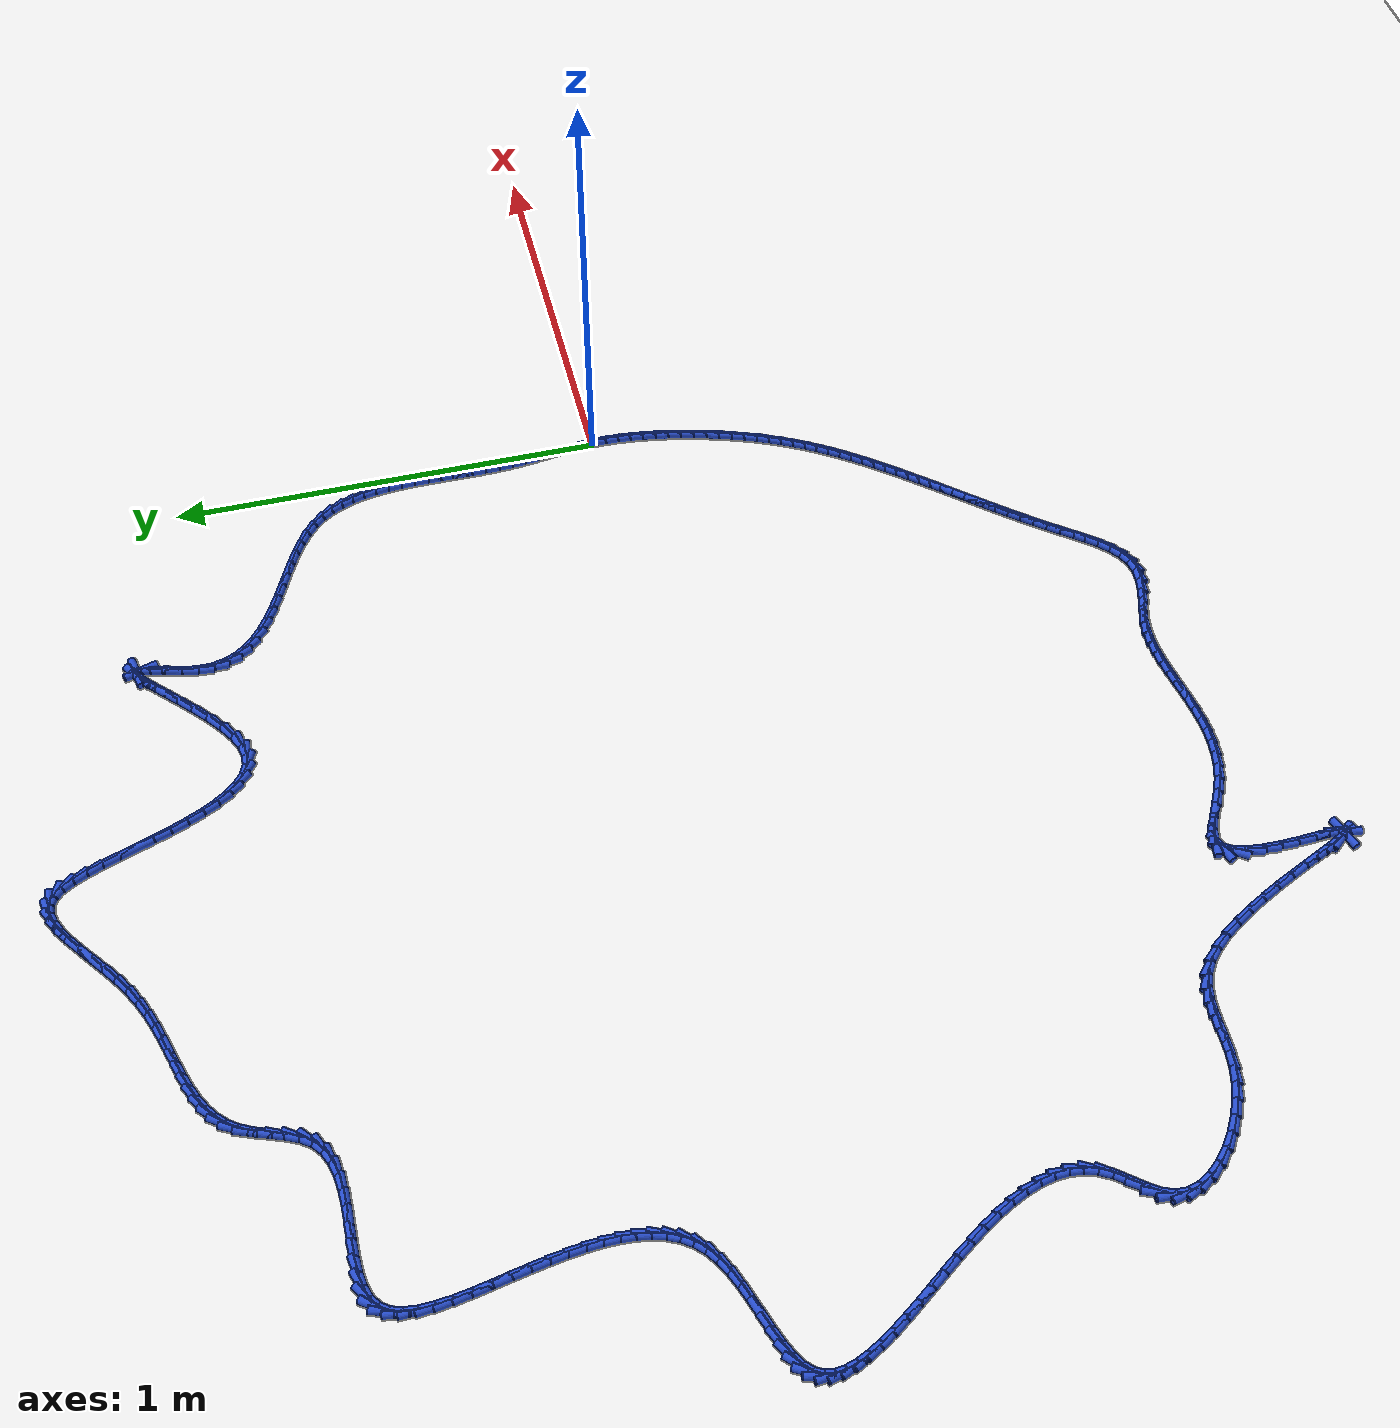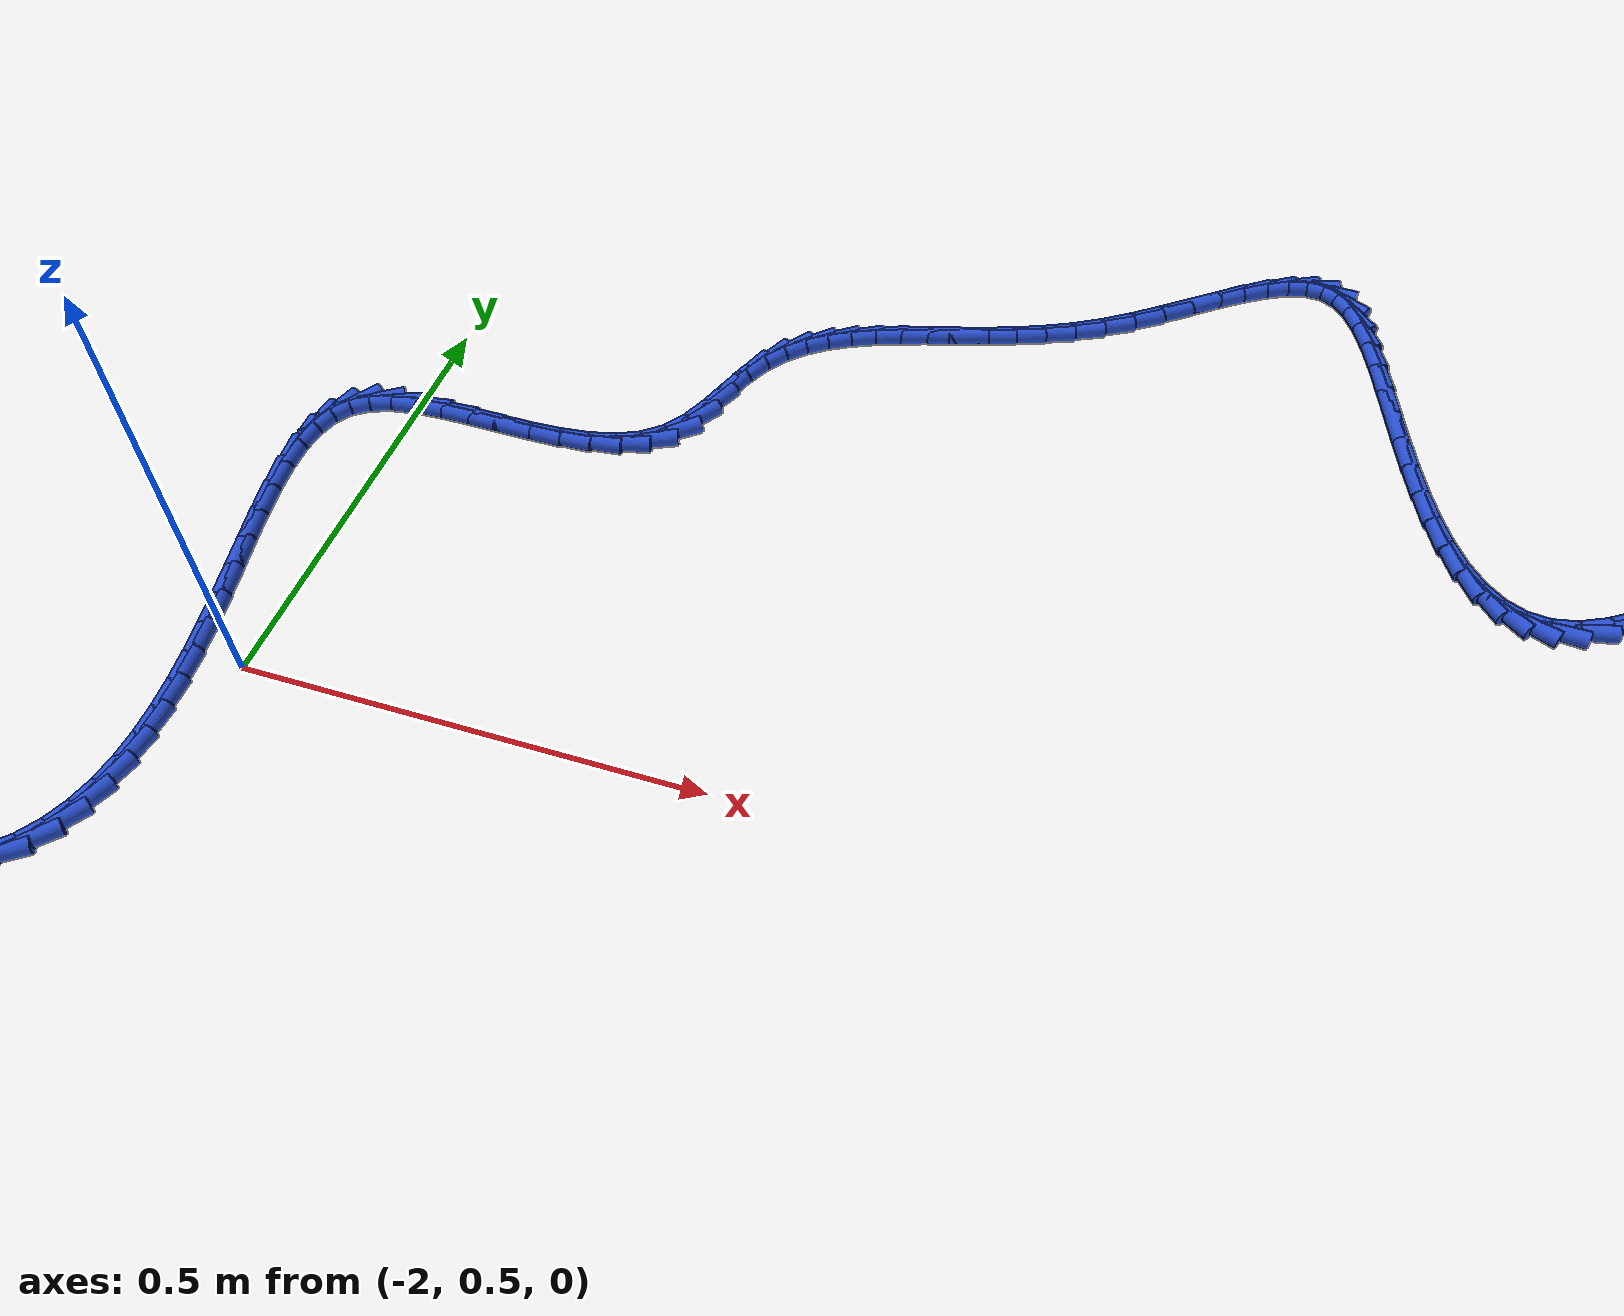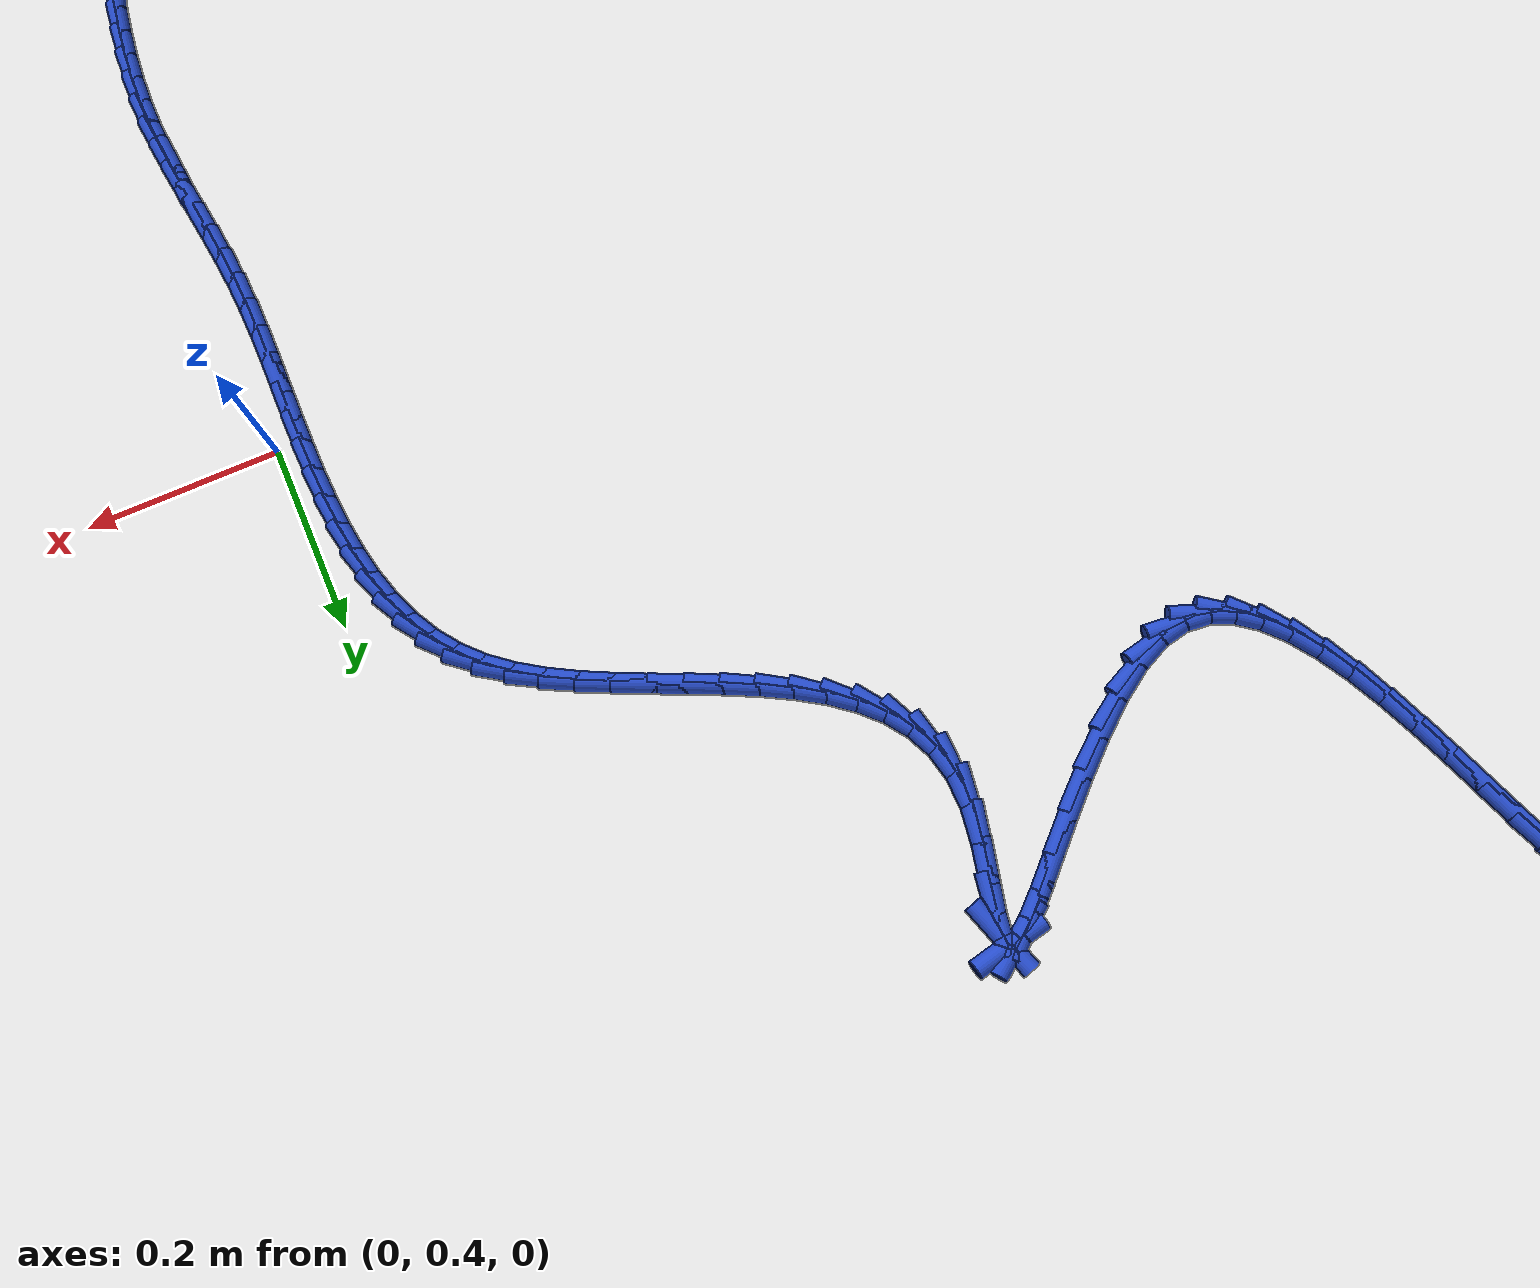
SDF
<sdf version="1.6">
 <world name="default">
  <light name="sun" type="directional">
   <pose>0 0 10 0 -0 0</pose>
   <diffuse>0.8 0.8 0.8 1</diffuse>
   <specular>0.2 0.2 0.2 1</specular>
   <attenuation>
    <range>1000</range>
    <constant>0.9</constant>
    <linear>0.01</linear>
    <quadratic>0.001</quadratic>
   </attenuation>
   <direction>-0.5 0.1 -0.9</direction>
  </light>
  <model name="ground_plane">
   <static>1</static>
   <link name="link">
    <collision name="collision">
     <geometry><plane><normal>0 0 1</normal><size>100 100</size></plane></geometry>
     <surface><friction><ode><mu>100</mu><mu2>50</mu2></ode></friction></surface>
    </collision>
    <visual name="visual">
     <cast_shadows>0</cast_shadows>
     <geometry><plane><normal>0 0 1</normal><size>100 100</size></plane></geometry>
     <material>
      <script><uri>file://media/materials/scripts/gazebo.material</uri><name>Gazebo/WhiteGlow</name></script>
     </material>
    </visual>
   </link>
  </model>
  <gravity>0 0 -9.8</gravity>
  <magnetic_field>6e-06 2.3e-05 -4.2e-05</magnetic_field>
  <atmosphere type="adiabatic"/>
  <physics name="default_physics" default="0" type="ode">
   <max_step_size>0.001</max_step_size>
   <real_time_factor>1</real_time_factor>
   <real_time_update_rate>1000</real_time_update_rate>
  </physics>
  <scene><ambient>0.4 0.4 0.4 1</ambient><background>0.7 0.7 0.7 1</background><shadows>1</shadows></scene>
  <spherical_coordinates>
   <surface_model>EARTH_WGS84</surface_model>
   <latitude_deg>0</latitude_deg>
   <longitude_deg>0</longitude_deg>
   <elevation>0</elevation>
   <heading_deg>0</heading_deg>
  </spherical_coordinates>
  <model name="line">
   <link name="link_0">
    <pose>1.734723475976807e-18 -3.469446951953614e-17 0.01 0 1.57 -1.50605853895009</pose>
    <collision name="collision">
     <geometry><cylinder><radius>0.01</radius><length>0.08</length></cylinder></geometry>
    </collision>
    <visual name="visual">
     <material>
      <script><name>Gazebo/Blue</name><uri>file://media/materials/scripts/gazebo.material</uri></script>
     </material>
     <geometry><cylinder><radius>0.01</radius><length>0.08</length></cylinder></geometry>
    </visual>
   </link>
   <link name="link_1">
    <pose>-0.001937820754875449 0.029891550811262525 0.01 0 1.57 -1.4679281092160998</pose>
    <collision name="collision">
     <geometry><cylinder><radius>0.01</radius><length>0.08</length></cylinder></geometry>
    </collision>
    <visual name="visual">
     <material>
      <script><name>Gazebo/Blue</name><uri>file://media/materials/scripts/gazebo.material</uri></script>
     </material>
     <geometry><cylinder><radius>0.01</radius><length>0.08</length></cylinder></geometry>
    </visual>
   </link>
   <link name="link_2">
    <pose>-0.00501331716304407 0.059683459835594886 0.01 0 1.57 -1.442875377174035</pose>
    <collision name="collision">
     <geometry><cylinder><radius>0.01</radius><length>0.08</length></cylinder></geometry>
    </collision>
    <visual name="visual">
     <material>
      <script><name>Gazebo/Blue</name><uri>file://media/materials/scripts/gazebo.material</uri></script>
     </material>
     <geometry><cylinder><radius>0.01</radius><length>0.08</length></cylinder></geometry>
    </visual>
   </link>
   <link name="link_3">
    <pose>-0.008849241074130565 0.08950639086981199 0.01 0 1.57 -1.4310051539160469</pose>
    <collision name="collision">
     <geometry><cylinder><radius>0.01</radius><length>0.08</length></cylinder></geometry>
    </collision>
    <visual name="visual">
     <material>
      <script><name>Gazebo/Blue</name><uri>file://media/materials/scripts/gazebo.material</uri></script>
     </material>
     <geometry><cylinder><radius>0.01</radius><length>0.08</length></cylinder></geometry>
    </visual>
   </link>
   <link name="link_4">
    <pose>-0.013068344337759637 0.11949100771072883 0.01 0 1.57 -1.4321455267452092</pose>
    <collision name="collision">
     <geometry><cylinder><radius>0.01</radius><length>0.08</length></cylinder></geometry>
    </collision>
    <visual name="visual">
     <material>
      <script><name>Gazebo/Blue</name><uri>file://media/materials/scripts/gazebo.material</uri></script>
     </material>
     <geometry><cylinder><radius>0.01</radius><length>0.08</length></cylinder></geometry>
    </visual>
   </link>
   <link name="link_5">
    <pose>-0.017293378803556 0.14976797415516044 0.01 0 1.57 -1.445921154118871</pose>
    <collision name="collision">
     <geometry><cylinder><radius>0.01</radius><length>0.08</length></cylinder></geometry>
    </collision>
    <visual name="visual">
     <material>
      <script><name>Gazebo/Blue</name><uri>file://media/materials/scripts/gazebo.material</uri></script>
     </material>
     <geometry><cylinder><radius>0.01</radius><length>0.08</length></cylinder></geometry>
    </visual>
   </link>
   <link name="link_6">
    <pose>-0.02114709632114435 0.18046795399992172 0.01 0 1.57 -1.471768061203181</pose>
    <collision name="collision">
     <geometry><cylinder><radius>0.01</radius><length>0.08</length></cylinder></geometry>
    </collision>
    <visual name="visual">
     <material>
      <script><name>Gazebo/Blue</name><uri>file://media/materials/scripts/gazebo.material</uri></script>
     </material>
     <geometry><cylinder><radius>0.01</radius><length>0.08</length></cylinder></geometry>
    </visual>
   </link>
   <link name="link_7">
    <pose>-0.0242522487401494 0.21172161104182766 0.01 0 1.57 -1.5078299508047135</pose>
    <collision name="collision">
     <geometry><cylinder><radius>0.01</radius><length>0.08</length></cylinder></geometry>
    </collision>
    <visual name="visual">
     <material>
      <script><name>Gazebo/Blue</name><uri>file://media/materials/scripts/gazebo.material</uri></script>
     </material>
     <geometry><cylinder><radius>0.01</radius><length>0.08</length></cylinder></geometry>
    </visual>
   </link>
   <link name="link_8">
    <pose>-0.026264977510847408 0.24364449110612799 0.01 0 1.57 -1.540823182527928</pose>
    <collision name="collision">
     <geometry><cylinder><radius>0.01</radius><length>0.08</length></cylinder></geometry>
    </collision>
    <visual name="visual">
     <material>
      <script><name>Gazebo/Blue</name><uri>file://media/materials/scripts/gazebo.material</uri></script>
     </material>
     <geometry><cylinder><radius>0.01</radius><length>0.08</length></cylinder></geometry>
    </visual>
   </link>
   <link name="link_9">
    <pose>-0.027240208713082564 0.27617158036557987 0.01 0 1.57 -1.5630544737676968</pose>
    <collision name="collision">
     <geometry><cylinder><radius>0.01</radius><length>0.08</length></cylinder></geometry>
    </collision>
    <visual name="visual">
     <material>
      <script><name>Gazebo/Blue</name><uri>file://media/materials/scripts/gazebo.material</uri></script>
     </material>
     <geometry><cylinder><radius>0.01</radius><length>0.08</length></cylinder></geometry>
    </visual>
   </link>
   <link name="link_10">
    <pose>-0.027495288260476734 0.3091190478909748 0.01 0 1.57 1.566483291200255</pose>
    <collision name="collision">
     <geometry><cylinder><radius>0.01</radius><length>0.08</length></cylinder></geometry>
    </collision>
    <visual name="visual">
     <material>
      <script><name>Gazebo/Blue</name><uri>file://media/materials/scripts/gazebo.material</uri></script>
     </material>
     <geometry><cylinder><radius>0.01</radius><length>0.08</length></cylinder></geometry>
    </visual>
   </link>
   <link name="link_11">
    <pose>-0.02735217253926407 0.342300975247039 0.01 0 1.57 1.5641954142616727</pose>
    <collision name="collision">
     <geometry><cylinder><radius>0.01</radius><length>0.08</length></cylinder></geometry>
    </collision>
    <visual name="visual">
     <material>
      <script><name>Gazebo/Blue</name><uri>file://media/materials/scripts/gazebo.material</uri></script>
     </material>
     <geometry><cylinder><radius>0.01</radius><length>0.08</length></cylinder></geometry>
    </visual>
   </link>
   <link name="link_12">
    <pose>-0.02713281793567875 0.37553144399849886 0.01 0 1.57 -1.569999698455388</pose>
    <collision name="collision">
     <geometry><cylinder><radius>0.01</radius><length>0.08</length></cylinder></geometry>
    </collision>
    <visual name="visual">
     <material>
      <script><name>Gazebo/Blue</name><uri>file://media/materials/scripts/gazebo.material</uri></script>
     </material>
     <geometry><cylinder><radius>0.01</radius><length>0.08</length></cylinder></geometry>
    </visual>
   </link>
   <link name="link_13">
    <pose>-0.02715918083595494 0.40862453571008106 0.01 0 1.57 -1.5526707415657952</pose>
    <collision name="collision">
     <geometry><cylinder><radius>0.01</radius><length>0.08</length></cylinder></geometry>
    </collision>
    <visual name="visual">
     <material>
      <script><name>Gazebo/Blue</name><uri>file://media/materials/scripts/gazebo.material</uri></script>
     </material>
     <geometry><cylinder><radius>0.01</radius><length>0.08</length></cylinder></geometry>
    </visual>
   </link>
   <link name="link_14">
    <pose>-0.02775321762632684 0.44139433194651195 0.01 0 1.57 -1.524838620631426</pose>
    <collision name="collision">
     <geometry><cylinder><radius>0.01</radius><length>0.08</length></cylinder></geometry>
    </collision>
    <visual name="visual">
     <material>
      <script><name>Gazebo/Blue</name><uri>file://media/materials/scripts/gazebo.material</uri></script>
     </material>
     <geometry><cylinder><radius>0.01</radius><length>0.08</length></cylinder></geometry>
    </visual>
   </link>
   <link name="link_15">
    <pose>-0.029236884693028597 0.473654914272518 0.01 0 1.57 -1.4856167380807048</pose>
    <collision name="collision">
     <geometry><cylinder><radius>0.01</radius><length>0.08</length></cylinder></geometry>
    </collision>
    <visual name="visual">
     <material>
      <script><name>Gazebo/Blue</name><uri>file://media/materials/scripts/gazebo.material</uri></script>
     </material>
     <geometry><cylinder><radius>0.01</radius><length>0.08</length></cylinder></geometry>
    </visual>
   </link>
   <link name="link_16">
    <pose>-0.03193213842229442 0.5052203642528259 0.01 0 1.57 -1.433843181203059</pose>
    <collision name="collision">
     <geometry><cylinder><radius>0.01</radius><length>0.08</length></cylinder></geometry>
    </collision>
    <visual name="visual">
     <material>
      <script><name>Gazebo/Blue</name><uri>file://media/materials/scripts/gazebo.material</uri></script>
     </material>
     <geometry><cylinder><radius>0.01</radius><length>0.08</length></cylinder></geometry>
    </visual>
   </link>
   <link name="link_17">
    <pose>-0.03616093520035844 0.5359047634521618 0.01 0 1.57 -1.3681855094326978</pose>
    <collision name="collision">
     <geometry><cylinder><radius>0.01</radius><length>0.08</length></cylinder></geometry>
    </collision>
    <visual name="visual">
     <material>
      <script><name>Gazebo/Blue</name><uri>file://media/materials/scripts/gazebo.material</uri></script>
     </material>
     <geometry><cylinder><radius>0.01</radius><length>0.08</length></cylinder></geometry>
    </visual>
   </link>
   <link name="link_18">
    <pose>-0.04224523141345487 0.5655221934352526 0.01 0 1.57 -1.287367441417076</pose>
    <collision name="collision">
     <geometry><cylinder><radius>0.01</radius><length>0.08</length></cylinder></geometry>
    </collision>
    <visual name="visual">
     <material>
      <script><name>Gazebo/Blue</name><uri>file://media/materials/scripts/gazebo.material</uri></script>
     </material>
     <geometry><cylinder><radius>0.01</radius><length>0.08</length></cylinder></geometry>
    </visual>
   </link>
   <link name="link_19">
    <pose>-0.05050698344781786 0.593886735766824 0.01 0 1.57 -1.1905823030846974</pose>
    <collision name="collision">
     <geometry><cylinder><radius>0.01</radius><length>0.08</length></cylinder></geometry>
    </collision>
    <visual name="visual">
     <material>
      <script><name>Gazebo/Blue</name><uri>file://media/materials/scripts/gazebo.material</uri></script>
     </material>
     <geometry><cylinder><radius>0.01</radius><length>0.08</length></cylinder></geometry>
    </visual>
   </link>
   <link name="link_20">
    <pose>-0.06126814768968159 0.6208124720116035 0.01 0 1.57 -1.0781147842913603</pose>
    <collision name="collision">
     <geometry><cylinder><radius>0.01</radius><length>0.08</length></cylinder></geometry>
    </collision>
    <visual name="visual">
     <material>
      <script><name>Gazebo/Blue</name><uri>file://media/materials/scripts/gazebo.material</uri></script>
     </material>
     <geometry><cylinder><radius>0.01</radius><length>0.08</length></cylinder></geometry>
    </visual>
   </link>
   <link name="link_21">
    <pose>-0.07485068052528027 0.6461134837343169 0.01 0 1.57 -0.9520417857666799</pose>
    <collision name="collision">
     <geometry><cylinder><radius>0.01</radius><length>0.08</length></cylinder></geometry>
    </collision>
    <visual name="visual">
     <material>
      <script><name>Gazebo/Blue</name><uri>file://media/materials/scripts/gazebo.material</uri></script>
     </material>
     <geometry><cylinder><radius>0.01</radius><length>0.08</length></cylinder></geometry>
    </visual>
   </link>
   <link name="link_22">
    <pose>-0.09157653834084803 0.6696038524996908 0.01 0 1.57 -0.8166756829383677</pose>
    <collision name="collision">
     <geometry><cylinder><radius>0.01</radius><length>0.08</length></cylinder></geometry>
    </collision>
    <visual name="visual">
     <material>
      <script><name>Gazebo/Blue</name><uri>file://media/materials/scripts/gazebo.material</uri></script>
     </material>
     <geometry><cylinder><radius>0.01</radius><length>0.08</length></cylinder></geometry>
    </visual>
   </link>
   <link name="link_23">
    <pose>-0.1117666952873153 0.6910982234052239 0.01 0 1.57 -0.6873337645888159</pose>
    <collision name="collision">
     <geometry><cylinder><radius>0.01</radius><length>0.08</length></cylinder></geometry>
    </collision>
    <visual name="visual">
     <material>
      <script><name>Gazebo/Blue</name><uri>file://media/materials/scripts/gazebo.material</uri></script>
     </material>
     <geometry><cylinder><radius>0.01</radius><length>0.08</length></cylinder></geometry>
    </visual>
   </link>
   <link name="link_24">
    <pose>-0.13547857977845482 0.710562444278915 0.01 0 1.57 -0.5872813566858414</pose>
    <collision name="collision">
     <geometry><cylinder><radius>0.01</radius><length>0.08</length></cylinder></geometry>
    </collision>
    <visual name="visual">
     <material>
      <script><name>Gazebo/Blue</name><uri>file://media/materials/scripts/gazebo.material</uri></script>
     </material>
     <geometry><cylinder><radius>0.01</radius><length>0.08</length></cylinder></geometry>
    </visual>
   </link>
   <link name="link_25">
    <pose>-0.16215180443155472 0.7283168192051274 0.01 0 1.57 -0.5152956075771535</pose>
    <collision name="collision">
     <geometry><cylinder><radius>0.01</radius><length>0.08</length></cylinder></geometry>
    </collision>
    <visual name="visual">
     <material>
      <script><name>Gazebo/Blue</name><uri>file://media/materials/scripts/gazebo.material</uri></script>
     </material>
     <geometry><cylinder><radius>0.01</radius><length>0.08</length></cylinder></geometry>
    </visual>
   </link>
   <link name="link_26">
    <pose>-0.1911375631079629 0.7447323803030238 0.01 0 1.57 -0.4668538863369033</pose>
    <collision name="collision">
     <geometry><cylinder><radius>0.01</radius><length>0.08</length></cylinder></geometry>
    </collision>
    <visual name="visual">
     <material>
      <script><name>Gazebo/Blue</name><uri>file://media/materials/scripts/gazebo.material</uri></script>
     </material>
     <geometry><cylinder><radius>0.01</radius><length>0.08</length></cylinder></geometry>
    </visual>
   </link>
   <link name="link_27">
    <pose>-0.22178704966902724 0.7601801596917661 0.01 0 1.57 -0.43855243625468854</pose>
    <collision name="collision">
     <geometry><cylinder><radius>0.01</radius><length>0.08</length></cylinder></geometry>
    </collision>
    <visual name="visual">
     <material>
      <script><name>Gazebo/Blue</name><uri>file://media/materials/scripts/gazebo.material</uri></script>
     </material>
     <geometry><cylinder><radius>0.01</radius><length>0.08</length></cylinder></geometry>
    </visual>
   </link>
   <link name="link_28">
    <pose>-0.2534514579760957 0.7750311894905167 0.01 0 1.57 -0.42833343813962643</pose>
    <collision name="collision">
     <geometry><cylinder><radius>0.01</radius><length>0.08</length></cylinder></geometry>
    </collision>
    <visual name="visual">
     <material>
      <script><name>Gazebo/Blue</name><uri>file://media/materials/scripts/gazebo.material</uri></script>
     </material>
     <geometry><cylinder><radius>0.01</radius><length>0.08</length></cylinder></geometry>
    </visual>
   </link>
   <link name="link_29">
    <pose>-0.28548198189051627 0.7896565018184383 0.01 0 1.57 -0.43546184774103414</pose>
    <collision name="collision">
     <geometry><cylinder><radius>0.01</radius><length>0.08</length></cylinder></geometry>
    </collision>
    <visual name="visual">
     <material>
      <script><name>Gazebo/Blue</name><uri>file://media/materials/scripts/gazebo.material</uri></script>
     </material>
     <geometry><cylinder><radius>0.01</radius><length>0.08</length></cylinder></geometry>
    </visual>
   </link>
   <link name="link_30">
    <pose>-0.31722981527363675 0.8044271287946925 0.01 0 1.57 -0.4604964189956765</pose>
    <collision name="collision">
     <geometry><cylinder><radius>0.01</radius><length>0.08</length></cylinder></geometry>
    </collision>
    <visual name="visual">
     <material>
      <script><name>Gazebo/Blue</name><uri>file://media/materials/scripts/gazebo.material</uri></script>
     </material>
     <geometry><cylinder><radius>0.01</radius><length>0.08</length></cylinder></geometry>
    </visual>
   </link>
   <link name="link_31">
    <pose>-0.3480461519868053 0.8197141025384421 0.01 0 1.57 -0.5053223352353128</pose>
    <collision name="collision">
     <geometry><cylinder><radius>0.01</radius><length>0.08</length></cylinder></geometry>
    </collision>
    <visual name="visual">
     <material>
      <script><name>Gazebo/Blue</name><uri>file://media/materials/scripts/gazebo.material</uri></script>
     </material>
     <geometry><cylinder><radius>0.01</radius><length>0.08</length></cylinder></geometry>
    </visual>
   </link>
   <link name="link_32">
    <pose>-0.3772821858913696 0.8358884551688491 0.01 0 1.57 -0.5731998730482989</pose>
    <collision name="collision">
     <geometry><cylinder><radius>0.01</radius><length>0.08</length></cylinder></geometry>
    </collision>
    <visual name="visual">
     <material>
      <script><name>Gazebo/Blue</name><uri>file://media/materials/scripts/gazebo.material</uri></script>
     </material>
     <geometry><cylinder><radius>0.01</radius><length>0.08</length></cylinder></geometry>
    </visual>
   </link>
   <link name="link_33">
    <pose>-0.4042891108486777 0.8533212188050762 0.01 0 1.57 -0.6686209416563463</pose>
    <collision name="collision">
     <geometry><cylinder><radius>0.01</radius><length>0.08</length></cylinder></geometry>
    </collision>
    <visual name="visual">
     <material>
      <script><name>Gazebo/Blue</name><uri>file://media/materials/scripts/gazebo.material</uri></script>
     </material>
     <geometry><cylinder><radius>0.01</radius><length>0.08</length></cylinder></geometry>
    </visual>
   </link>
   <link name="link_34">
    <pose>-0.4284181207200775 0.8723834255662852 0.01 0 1.57 -0.79644760408248</pose>
    <collision name="collision">
     <geometry><cylinder><radius>0.01</radius><length>0.08</length></cylinder></geometry>
    </collision>
    <visual name="visual">
     <material>
      <script><name>Gazebo/Blue</name><uri>file://media/materials/scripts/gazebo.material</uri></script>
     </material>
     <geometry><cylinder><radius>0.01</radius><length>0.08</length></cylinder></geometry>
    </visual>
   </link>
   <link name="link_35">
    <pose>-0.4490204093669169 0.8934461075716386 0.01 0 1.57 -0.9594168607564313</pose>
    <collision name="collision">
     <geometry><cylinder><radius>0.01</radius><length>0.08</length></cylinder></geometry>
    </collision>
    <visual name="visual">
     <material>
      <script><name>Gazebo/Blue</name><uri>file://media/materials/scripts/gazebo.material</uri></script>
     </material>
     <geometry><cylinder><radius>0.01</radius><length>0.08</length></cylinder></geometry>
    </visual>
   </link>
   <link name="link_36">
    <pose>-0.46544717065054375 0.9168802969402987 0.01 0 1.57 -1.1535828660022822</pose>
    <collision name="collision">
     <geometry><cylinder><radius>0.01</radius><length>0.08</length></cylinder></geometry>
    </collision>
    <visual name="visual">
     <material>
      <script><name>Gazebo/Blue</name><uri>file://media/materials/scripts/gazebo.material</uri></script>
     </material>
     <geometry><cylinder><radius>0.01</radius><length>0.08</length></cylinder></geometry>
    </visual>
   </link>
   <link name="link_37">
    <pose>-0.4770495984323062 0.9430570257914278 0.01 0 1.57 -1.364512986633252</pose>
    <collision name="collision">
     <geometry><cylinder><radius>0.01</radius><length>0.08</length></cylinder></geometry>
    </collision>
    <visual name="visual">
     <material>
      <script><name>Gazebo/Blue</name><uri>file://media/materials/scripts/gazebo.material</uri></script>
     </material>
     <geometry><cylinder><radius>0.01</radius><length>0.08</length></cylinder></geometry>
    </visual>
   </link>
   <link name="link_38">
    <pose>-0.4831788865735521 0.9723473262441882 0.01 0 1.57 -1.5704683569661182</pose>
    <collision name="collision">
     <geometry><cylinder><radius>0.01</radius><length>0.08</length></cylinder></geometry>
    </collision>
    <visual name="visual">
     <material>
      <script><name>Gazebo/Blue</name><uri>file://media/materials/scripts/gazebo.material</uri></script>
     </material>
     <geometry><cylinder><radius>0.01</radius><length>0.08</length></cylinder></geometry>
    </visual>
   </link>
   <link name="link_39">
    <pose>-0.4831896345588908 1.005118587531682 0.01 0 1.57 1.4116530401254945</pose>
    <collision name="collision">
     <geometry><cylinder><radius>0.01</radius><length>0.08</length></cylinder></geometry>
    </collision>
    <visual name="visual">
     <material>
      <script><name>Gazebo/Blue</name><uri>file://media/materials/scripts/gazebo.material</uri></script>
     </material>
     <geometry><cylinder><radius>0.01</radius><length>0.08</length></cylinder></geometry>
    </visual>
   </link>
   <link name="link_40">
    <pose>-0.47749367470440174 1.0406073108091247 0.01 0 1.57 1.33227171243182</pose>
    <collision name="collision">
     <geometry><cylinder><radius>0.01</radius><length>0.08</length></cylinder></geometry>
    </collision>
    <visual name="visual">
     <material>
      <script><name>Gazebo/Blue</name><uri>file://media/materials/scripts/gazebo.material</uri></script>
     </material>
     <geometry><cylinder><radius>0.01</radius><length>0.08</length></cylinder></geometry>
    </visual>
   </link>
   <link name="link_41">
    <pose>-0.46905250509312907 1.0753227014718703 0.01 0 1.57 1.3153170209641836</pose>
    <collision name="collision">
     <geometry><cylinder><radius>0.01</radius><length>0.08</length></cylinder></geometry>
    </collision>
    <visual name="visual">
     <material>
      <script><name>Gazebo/Blue</name><uri>file://media/materials/scripts/gazebo.material</uri></script>
     </material>
     <geometry><cylinder><radius>0.01</radius><length>0.08</length></cylinder></geometry>
    </visual>
   </link>
   <link name="link_42">
    <pose>-0.46120426765963307 1.1053710810578947 0.01 0 1.57 1.3904783841975357</pose>
    <collision name="collision">
     <geometry><cylinder><radius>0.01</radius><length>0.08</length></cylinder></geometry>
    </collision>
    <visual name="visual">
     <material>
      <script><name>Gazebo/Blue</name><uri>file://media/materials/scripts/gazebo.material</uri></script>
     </material>
     <geometry><cylinder><radius>0.01</radius><length>0.08</length></cylinder></geometry>
    </visual>
   </link>
   <link name="link_43">
    <pose>-0.4572871043384739 1.1268587711051745 0.01 0 1.57 -1.2693166915440863</pose>
    <collision name="collision">
     <geometry><cylinder><radius>0.01</radius><length>0.08</length></cylinder></geometry>
    </collision>
    <visual name="visual">
     <material>
      <script><name>Gazebo/Blue</name><uri>file://media/materials/scripts/gazebo.material</uri></script>
     </material>
     <geometry><cylinder><radius>0.01</radius><length>0.08</length></cylinder></geometry>
    </visual>
   </link>
   <link name="link_44">
    <pose>-0.4602591427514989 1.1364164489141484 0.01 0 1.57 0.19368764389536142</pose>
    <collision name="collision">
     <geometry><cylinder><radius>0.01</radius><length>0.08</length></cylinder></geometry>
    </collision>
    <visual name="visual">
     <material>
      <script><name>Gazebo/Blue</name><uri>file://media/materials/scripts/gazebo.material</uri></script>
     </material>
     <geometry><cylinder><radius>0.01</radius><length>0.08</length></cylinder></geometry>
    </visual>
   </link>
   <link name="link_45">
    <pose>-0.47035212502581486 1.1344367446829082 0.01 0 1.57 0.6149706926015445</pose>
    <collision name="collision">
     <geometry><cylinder><radius>0.01</radius><length>0.08</length></cylinder></geometry>
    </collision>
    <visual name="visual">
     <material>
      <script><name>Gazebo/Blue</name><uri>file://media/materials/scripts/gazebo.material</uri></script>
     </material>
     <geometry><cylinder><radius>0.01</radius><length>0.08</length></cylinder></geometry>
    </visual>
   </link>
   <link name="link_46">
    <pose>-0.4866072434327489 1.1229550469386202 0.01 0 1.57 0.7232912617935959</pose>
    <collision name="collision">
     <geometry><cylinder><radius>0.01</radius><length>0.08</length></cylinder></geometry>
    </collision>
    <visual name="visual">
     <material>
      <script><name>Gazebo/Blue</name><uri>file://media/materials/scripts/gazebo.material</uri></script>
     </material>
     <geometry><cylinder><radius>0.01</radius><length>0.08</length></cylinder></geometry>
    </visual>
   </link>
   <link name="link_47">
    <pose>-0.5080607159211911 1.1040136079358085 0.01 0 1.57 0.7588470234525712</pose>
    <collision name="collision">
     <geometry><cylinder><radius>0.01</radius><length>0.08</length></cylinder></geometry>
    </collision>
    <visual name="visual">
     <material>
      <script><name>Gazebo/Blue</name><uri>file://media/materials/scripts/gazebo.material</uri></script>
     </material>
     <geometry><cylinder><radius>0.01</radius><length>0.08</length></cylinder></geometry>
    </visual>
   </link>
   <link name="link_48">
    <pose>-0.5337487604400319 1.0796546799289954 0.01 0 1.57 0.7637997417366655</pose>
    <collision name="collision">
     <geometry><cylinder><radius>0.01</radius><length>0.08</length></cylinder></geometry>
    </collision>
    <visual name="visual">
     <material>
      <script><name>Gazebo/Blue</name><uri>file://media/materials/scripts/gazebo.material</uri></script>
     </material>
     <geometry><cylinder><radius>0.01</radius><length>0.08</length></cylinder></geometry>
    </visual>
   </link>
   <link name="link_49">
    <pose>-0.5627075949381609 1.0519205151727054 0.01 0 1.57 0.7489716486077683</pose>
    <collision name="collision">
     <geometry><cylinder><radius>0.01</radius><length>0.08</length></cylinder></geometry>
    </collision>
    <visual name="visual">
     <material>
      <script><name>Gazebo/Blue</name><uri>file://media/materials/scripts/gazebo.material</uri></script>
     </material>
     <geometry><cylinder><radius>0.01</radius><length>0.08</length></cylinder></geometry>
    </visual>
   </link>
   <link name="link_50">
    <pose>-0.5939734373644687 1.0228533659214614 0.01 0 1.57 0.7157814802865851</pose>
    <collision name="collision">
     <geometry><cylinder><radius>0.01</radius><length>0.08</length></cylinder></geometry>
    </collision>
    <visual name="visual">
     <material>
      <script><name>Gazebo/Blue</name><uri>file://media/materials/scripts/gazebo.material</uri></script>
     </material>
     <geometry><cylinder><radius>0.01</radius><length>0.08</length></cylinder></geometry>
    </visual>
   </link>
   <link name="link_51">
    <pose>-0.6265825056678449 0.9944954844297867 0.01 0 1.57 0.6600721721788052</pose>
    <collision name="collision">
     <geometry><cylinder><radius>0.01</radius><length>0.08</length></cylinder></geometry>
    </collision>
    <visual name="visual">
     <material>
      <script><name>Gazebo/Blue</name><uri>file://media/materials/scripts/gazebo.material</uri></script>
     </material>
     <geometry><cylinder><radius>0.01</radius><length>0.08</length></cylinder></geometry>
    </visual>
   </link>
   <link name="link_52">
    <pose>-0.6595710177971802 0.9688891229522046 0.01 0 1.57 0.5709297922830731</pose>
    <collision name="collision">
     <geometry><cylinder><radius>0.01</radius><length>0.08</length></cylinder></geometry>
    </collision>
    <visual name="visual">
     <material>
      <script><name>Gazebo/Blue</name><uri>file://media/materials/scripts/gazebo.material</uri></script>
     </material>
     <geometry><cylinder><radius>0.01</radius><length>0.08</length></cylinder></geometry>
    </visual>
   </link>
   <link name="link_53">
    <pose>-0.6919751917013639 0.9480765337432386 0.01 0 1.57 0.4253129144393534</pose>
    <collision name="collision">
     <geometry><cylinder><radius>0.01</radius><length>0.08</length></cylinder></geometry>
    </collision>
    <visual name="visual">
     <material>
      <script><name>Gazebo/Blue</name><uri>file://media/materials/scripts/gazebo.material</uri></script>
     </material>
     <geometry><cylinder><radius>0.01</radius><length>0.08</length></cylinder></geometry>
    </visual>
   </link>
   <link name="link_54">
    <pose>-0.7228312453292871 0.9340999690574125 0.01 0 1.57 0.19012810390382626</pose>
    <collision name="collision">
     <geometry><cylinder><radius>0.01</radius><length>0.08</length></cylinder></geometry>
    </collision>
    <visual name="visual">
     <material>
      <script><name>Gazebo/Blue</name><uri>file://media/materials/scripts/gazebo.material</uri></script>
     </material>
     <geometry><cylinder><radius>0.01</radius><length>0.08</length></cylinder></geometry>
    </visual>
   </link>
   <link name="link_55">
    <pose>-0.7513303389363087 0.928615242032474 0.01 0 1.57 -0.10456611202650012</pose>
    <collision name="collision">
     <geometry><cylinder><radius>0.01</radius><length>0.08</length></cylinder></geometry>
    </collision>
    <visual name="visual">
     <material>
      <script><name>Gazebo/Blue</name><uri>file://media/materials/scripts/gazebo.material</uri></script>
     </material>
     <geometry><cylinder><radius>0.01</radius><length>0.08</length></cylinder></geometry>
    </visual>
   </link>
   <link name="link_56">
    <pose>-0.7774347744485441 0.9313548737567285 0.01 0 1.57 -0.3996345137070338</pose>
    <collision name="collision">
     <geometry><cylinder><radius>0.01</radius><length>0.08</length></cylinder></geometry>
    </collision>
    <visual name="visual">
     <material>
      <script><name>Gazebo/Blue</name><uri>file://media/materials/scripts/gazebo.material</uri></script>
     </material>
     <geometry><cylinder><radius>0.01</radius><length>0.08</length></cylinder></geometry>
    </visual>
   </link>
   <link name="link_57">
    <pose>-0.8013462937270182 0.9414542020244201 0.01 0 1.57 -0.647978246161115</pose>
    <collision name="collision">
     <geometry><cylinder><radius>0.01</radius><length>0.08</length></cylinder></geometry>
    </collision>
    <visual name="visual">
     <material>
      <script><name>Gazebo/Blue</name><uri>file://media/materials/scripts/gazebo.material</uri></script>
     </material>
     <geometry><cylinder><radius>0.01</radius><length>0.08</length></cylinder></geometry>
    </visual>
   </link>
   <link name="link_58">
    <pose>-0.823266713033428 0.9580483790682687 0.01 0 1.57 -0.834774287737094</pose>
    <collision name="collision">
     <geometry><cylinder><radius>0.01</radius><length>0.08</length></cylinder></geometry>
    </collision>
    <visual name="visual">
     <material>
      <script><name>Gazebo/Blue</name><uri>file://media/materials/scripts/gazebo.material</uri></script>
     </material>
     <geometry><cylinder><radius>0.01</radius><length>0.08</length></cylinder></geometry>
    </visual>
   </link>
   <link name="link_59">
    <pose>-0.8433978486294715 0.9802725571209945 0.01 0 1.57 -0.968798302903361</pose>
    <collision name="collision">
     <geometry><cylinder><radius>0.01</radius><length>0.08</length></cylinder></geometry>
    </collision>
    <visual name="visual">
     <material>
      <script><name>Gazebo/Blue</name><uri>file://media/materials/scripts/gazebo.material</uri></script>
     </material>
     <geometry><cylinder><radius>0.01</radius><length>0.08</length></cylinder></geometry>
    </visual>
   </link>
   <link name="link_60">
    <pose>-0.8619415167768463 1.0072618884153177 0.01 0 1.57 -1.063769376628445</pose>
    <collision name="collision">
     <geometry><cylinder><radius>0.01</radius><length>0.08</length></cylinder></geometry>
    </collision>
    <visual name="visual">
     <material>
      <script><name>Gazebo/Blue</name><uri>file://media/materials/scripts/gazebo.material</uri></script>
     </material>
     <geometry><cylinder><radius>0.01</radius><length>0.08</length></cylinder></geometry>
    </visual>
   </link>
   <link name="link_61">
    <pose>-0.87909953373725 1.038151525183959 0.01 0 1.57 -1.1307261581408423</pose>
    <collision name="collision">
     <geometry><cylinder><radius>0.01</radius><length>0.08</length></cylinder></geometry>
    </collision>
    <visual name="visual">
     <material>
      <script><name>Gazebo/Blue</name><uri>file://media/materials/scripts/gazebo.material</uri></script>
     </material>
     <geometry><cylinder><radius>0.01</radius><length>0.08</length></cylinder></geometry>
    </visual>
   </link>
   <link name="link_62">
    <pose>-0.8950737157723798 1.072076619659638 0.01 0 1.57 -1.1771320540357002</pose>
    <collision name="collision">
     <geometry><cylinder><radius>0.01</radius><length>0.08</length></cylinder></geometry>
    </collision>
    <visual name="visual">
     <material>
      <script><name>Gazebo/Blue</name><uri>file://media/materials/scripts/gazebo.material</uri></script>
     </material>
     <geometry><cylinder><radius>0.01</radius><length>0.08</length></cylinder></geometry>
    </visual>
   </link>
   <link name="link_63">
    <pose>-0.910065879143934 1.1081723240750758 0.01 0 1.57 -1.2076632492249755</pose>
    <collision name="collision">
     <geometry><cylinder><radius>0.01</radius><length>0.08</length></cylinder></geometry>
    </collision>
    <visual name="visual">
     <material>
      <script><name>Gazebo/Blue</name><uri>file://media/materials/scripts/gazebo.material</uri></script>
     </material>
     <geometry><cylinder><radius>0.01</radius><length>0.08</length></cylinder></geometry>
    </visual>
   </link>
   <link name="link_64">
    <pose>-0.9242778401136098 1.145573790662992 0.01 0 1.57 -1.224999399807576</pose>
    <collision name="collision">
     <geometry><cylinder><radius>0.01</radius><length>0.08</length></cylinder></geometry>
    </collision>
    <visual name="visual">
     <material>
      <script><name>Gazebo/Blue</name><uri>file://media/materials/scripts/gazebo.material</uri></script>
     </material>
     <geometry><cylinder><radius>0.01</radius><length>0.08</length></cylinder></geometry>
    </visual>
   </link>
   <link name="link_65">
    <pose>-0.9379114149431049 1.183416171656107 0.01 0 1.57 -1.2302707892728297</pose>
    <collision name="collision">
     <geometry><cylinder><radius>0.01</radius><length>0.08</length></cylinder></geometry>
    </collision>
    <visual name="visual">
     <material>
      <script><name>Gazebo/Blue</name><uri>file://media/materials/scripts/gazebo.material</uri></script>
     </material>
     <geometry><cylinder><radius>0.01</radius><length>0.08</length></cylinder></geometry>
    </visual>
   </link>
   <link name="link_66">
    <pose>-0.951169213852165 1.220832882188781 0.01 0 1.57 -1.2201918504669882</pose>
    <collision name="collision">
     <geometry><cylinder><radius>0.01</radius><length>0.08</length></cylinder></geometry>
    </collision>
    <visual name="visual">
     <material>
      <script><name>Gazebo/Blue</name><uri>file://media/materials/scripts/gazebo.material</uri></script>
     </material>
     <geometry><cylinder><radius>0.01</radius><length>0.08</length></cylinder></geometry>
    </visual>
   </link>
   <link name="link_67">
    <pose>-0.9643241601935064 1.2568034995089359 0.01 0 1.57 -1.1862270527395904</pose>
    <collision name="collision">
     <geometry><cylinder><radius>0.01</radius><length>0.08</length></cylinder></geometry>
    </collision>
    <visual name="visual">
     <material>
      <script><name>Gazebo/Blue</name><uri>file://media/materials/scripts/gazebo.material</uri></script>
     </material>
     <geometry><cylinder><radius>0.01</radius><length>0.08</length></cylinder></geometry>
    </visual>
   </link>
   <link name="link_68">
    <pose>-0.977773699429289 1.2900351593258794 0.01 0 1.57 -1.1190553558282887</pose>
    <collision name="collision">
     <geometry><cylinder><radius>0.01</radius><length>0.08</length></cylinder></geometry>
    </collision>
    <visual name="visual">
     <material>
      <script><name>Gazebo/Blue</name><uri>file://media/materials/scripts/gazebo.material</uri></script>
     </material>
     <geometry><cylinder><radius>0.01</radius><length>0.08</length></cylinder></geometry>
    </visual>
   </link>
   <link name="link_69">
    <pose>-0.9919280357944591 1.319207082469351 0.01 0 1.57 -1.0002068482792532</pose>
    <collision name="collision">
     <geometry><cylinder><radius>0.01</radius><length>0.08</length></cylinder></geometry>
    </collision>
    <visual name="visual">
     <material>
      <script><name>Gazebo/Blue</name><uri>file://media/materials/scripts/gazebo.material</uri></script>
     </material>
     <geometry><cylinder><radius>0.01</radius><length>0.08</length></cylinder></geometry>
    </visual>
   </link>
   <link name="link_70">
    <pose>-1.0071973735239628 1.342998489769089 0.01 0 1.57 -0.7941207387226378</pose>
    <collision name="collision">
     <geometry><cylinder><radius>0.01</radius><length>0.08</length></cylinder></geometry>
    </collision>
    <visual name="visual">
     <material>
      <script><name>Gazebo/Blue</name><uri>file://media/materials/scripts/gazebo.material</uri></script>
     </material>
     <geometry><cylinder><radius>0.01</radius><length>0.08</length></cylinder></geometry>
    </visual>
   </link>
   <link name="link_71">
    <pose>-1.0239919168527458 1.3600886020548317 0.01 0 1.57 -0.4524726296850768</pose>
    <collision name="collision">
     <geometry><cylinder><radius>0.01</radius><length>0.08</length></cylinder></geometry>
    </collision>
    <visual name="visual">
     <material>
      <script><name>Gazebo/Blue</name><uri>file://media/materials/scripts/gazebo.material</uri></script>
     </material>
     <geometry><cylinder><radius>0.01</radius><length>0.08</length></cylinder></geometry>
    </visual>
   </link>
   <link name="link_72">
    <pose>-1.0427144453390609 1.3691897788714027 0.01 0 1.57 -0.04481095048637973</pose>
    <collision name="collision">
     <geometry><cylinder><radius>0.01</radius><length>0.08</length></cylinder></geometry>
    </collision>
    <visual name="visual">
     <material>
      <script><name>Gazebo/Blue</name><uri>file://media/materials/scripts/gazebo.material</uri></script>
     </material>
     <geometry><cylinder><radius>0.01</radius><length>0.08</length></cylinder></geometry>
    </visual>
   </link>
   <link name="link_73">
    <pose>-1.0635194224466509 1.3701226941919893 0.01 0 1.57 0.26088683718025485</pose>
    <collision name="collision">
     <geometry><cylinder><radius>0.01</radius><length>0.08</length></cylinder></geometry>
    </collision>
    <visual name="visual">
     <material>
      <script><name>Gazebo/Blue</name><uri>file://media/materials/scripts/gazebo.material</uri></script>
     </material>
     <geometry><cylinder><radius>0.01</radius><length>0.08</length></cylinder></geometry>
    </visual>
   </link>
   <link name="link_74">
    <pose>-1.086260300576472 1.3640515309743524 0.01 0 1.57 0.44965654378894504</pose>
    <collision name="collision">
     <geometry><cylinder><radius>0.01</radius><length>0.08</length></cylinder></geometry>
    </collision>
    <visual name="visual">
     <material>
      <script><name>Gazebo/Blue</name><uri>file://media/materials/scripts/gazebo.material</uri></script>
     </material>
     <geometry><cylinder><radius>0.01</radius><length>0.08</length></cylinder></geometry>
    </visual>
   </link>
   <link name="link_75">
    <pose>-1.1107724459546222 1.3522211965795166 0.01 0 1.57 0.5591597089260998</pose>
    <collision name="collision">
     <geometry><cylinder><radius>0.01</radius><length>0.08</length></cylinder></geometry>
    </collision>
    <visual name="visual">
     <material>
      <script><name>Gazebo/Blue</name><uri>file://media/materials/scripts/gazebo.material</uri></script>
     </material>
     <geometry><cylinder><radius>0.01</radius><length>0.08</length></cylinder></geometry>
    </visual>
   </link>
   <link name="link_76">
    <pose>-1.1368912248071987 1.3358765983685055 0.01 0 1.57 0.6185099055657508</pose>
    <collision name="collision">
     <geometry><cylinder><radius>0.01</radius><length>0.08</length></cylinder></geometry>
    </collision>
    <visual name="visual">
     <material>
      <script><name>Gazebo/Blue</name><uri>file://media/materials/scripts/gazebo.material</uri></script>
     </material>
     <geometry><cylinder><radius>0.01</radius><length>0.08</length></cylinder></geometry>
    </visual>
   </link>
   <link name="link_77">
    <pose>-1.1644520033602992 1.316262643702343 0.01 0 1.57 0.6437184609977504</pose>
    <collision name="collision">
     <geometry><cylinder><radius>0.01</radius><length>0.08</length></cylinder></geometry>
    </collision>
    <visual name="visual">
     <material>
      <script><name>Gazebo/Blue</name><uri>file://media/materials/scripts/gazebo.material</uri></script>
     </material>
     <geometry><cylinder><radius>0.01</radius><length>0.08</length></cylinder></geometry>
    </visual>
   </link>
   <link name="link_78">
    <pose>-1.1932901478400209 1.2946242399420533 0.01 0 1.57 0.642534304365859</pose>
    <collision name="collision">
     <geometry><cylinder><radius>0.01</radius><length>0.08</length></cylinder></geometry>
    </collision>
    <visual name="visual">
     <material>
      <script><name>Gazebo/Blue</name><uri>file://media/materials/scripts/gazebo.material</uri></script>
     </material>
     <geometry><cylinder><radius>0.01</radius><length>0.08</length></cylinder></geometry>
    </visual>
   </link>
   <link name="link_79">
    <pose>-1.2232410244724614 1.2722062944486607 0.01 0 1.57 0.6177136794814649</pose>
    <collision name="collision">
     <geometry><cylinder><radius>0.01</radius><length>0.08</length></cylinder></geometry>
    </collision>
    <visual name="visual">
     <material>
      <script><name>Gazebo/Blue</name><uri>file://media/materials/scripts/gazebo.material</uri></script>
     </material>
     <geometry><cylinder><radius>0.01</radius><length>0.08</length></cylinder></geometry>
    </visual>
   </link>
   <link name="link_80">
    <pose>-1.2541399994837183 1.2502537145831891 0.01 0 1.57 0.5685413186029408</pose>
    <collision name="collision">
     <geometry><cylinder><radius>0.01</radius><length>0.08</length></cylinder></geometry>
    </collision>
    <visual name="visual">
     <material>
      <script><name>Gazebo/Blue</name><uri>file://media/materials/scripts/gazebo.material</uri></script>
     </material>
     <geometry><cylinder><radius>0.01</radius><length>0.08</length></cylinder></geometry>
    </visual>
   </link>
   <link name="link_81">
    <pose>-1.2858224390998887 1.2300114077066628 0.01 0 1.57 0.49469715784250584</pose>
    <collision name="collision">
     <geometry><cylinder><radius>0.01</radius><length>0.08</length></cylinder></geometry>
    </collision>
    <visual name="visual">
     <material>
      <script><name>Gazebo/Blue</name><uri>file://media/materials/scripts/gazebo.material</uri></script>
     </material>
     <geometry><cylinder><radius>0.01</radius><length>0.08</length></cylinder></geometry>
    </visual>
   </link>
   <link name="link_82">
    <pose>-1.3181137801269582 1.212592268144459 0.01 0 1.57 0.4208073558974105</pose>
    <collision name="collision">
     <geometry><cylinder><radius>0.01</radius><length>0.08</length></cylinder></geometry>
    </collision>
    <visual name="visual">
     <material>
      <script><name>Gazebo/Blue</name><uri>file://media/materials/scripts/gazebo.material</uri></script>
     </material>
     <geometry><cylinder><radius>0.01</radius><length>0.08</length></cylinder></geometry>
    </visual>
   </link>
   <link name="link_83">
    <pose>-1.3507548315065803 1.197984050874085 0.01 0 1.57 0.3620019216211056</pose>
    <collision name="collision">
     <geometry><cylinder><radius>0.01</radius><length>0.08</length></cylinder></geometry>
    </collision>
    <visual name="visual">
     <material>
      <script><name>Gazebo/Blue</name><uri>file://media/materials/scripts/gazebo.material</uri></script>
     </material>
     <geometry><cylinder><radius>0.01</radius><length>0.08</length></cylinder></geometry>
    </visual>
   </link>
   <link name="link_84">
    <pose>-1.3834435771098041 1.185605145541716 0.01 0 1.57 0.3196472979774152</pose>
    <collision name="collision">
     <geometry><cylinder><radius>0.01</radius><length>0.08</length></cylinder></geometry>
    </collision>
    <visual name="visual">
     <material>
      <script><name>Gazebo/Blue</name><uri>file://media/materials/scripts/gazebo.material</uri></script>
     </material>
     <geometry><cylinder><radius>0.01</radius><length>0.08</length></cylinder></geometry>
    </visual>
   </link>
   <link name="link_85">
    <pose>-1.4158776686422627 1.17486952560765 0.01 0 1.57 0.2947699607814255</pose>
    <collision name="collision">
     <geometry><cylinder><radius>0.01</radius><length>0.08</length></cylinder></geometry>
    </collision>
    <visual name="visual">
     <material>
      <script><name>Gazebo/Blue</name><uri>file://media/materials/scripts/gazebo.material</uri></script>
     </material>
     <geometry><cylinder><radius>0.01</radius><length>0.08</length></cylinder></geometry>
    </visual>
   </link>
   <link name="link_86">
    <pose>-1.447754757809589 1.1651911645321853 0.01 0 1.57 0.2885499597719304</pose>
    <collision name="collision">
     <geometry><cylinder><radius>0.01</radius><length>0.08</length></cylinder></geometry>
    </collision>
    <visual name="visual">
     <material>
      <script><name>Gazebo/Blue</name><uri>file://media/materials/scripts/gazebo.material</uri></script>
     </material>
     <geometry><cylinder><radius>0.01</radius><length>0.08</length></cylinder></geometry>
    </visual>
   </link>
   <link name="link_87">
    <pose>-1.4787724963174167 1.155984035775621 0.01 0 1.57 0.302638008586667</pose>
    <collision name="collision">
     <geometry><cylinder><radius>0.01</radius><length>0.08</length></cylinder></geometry>
    </collision>
    <visual name="visual">
     <material>
      <script><name>Gazebo/Blue</name><uri>file://media/materials/scripts/gazebo.material</uri></script>
     </material>
     <geometry><cylinder><radius>0.01</radius><length>0.08</length></cylinder></geometry>
    </visual>
   </link>
   <link name="link_88">
    <pose>-1.5086285358713776 1.1466621127982555 0.01 0 1.57 0.33935652323841187</pose>
    <collision name="collision">
     <geometry><cylinder><radius>0.01</radius><length>0.08</length></cylinder></geometry>
    </collision>
    <visual name="visual">
     <material>
      <script><name>Gazebo/Blue</name><uri>file://media/materials/scripts/gazebo.material</uri></script>
     </material>
     <geometry><cylinder><radius>0.01</radius><length>0.08</length></cylinder></geometry>
    </visual>
   </link>
   <link name="link_89">
    <pose>-1.5370205281771048 1.1366393690603873 0.01 0 1.57 0.40167061080339866</pose>
    <collision name="collision">
     <geometry><cylinder><radius>0.01</radius><length>0.08</length></cylinder></geometry>
    </collision>
    <visual name="visual">
     <material>
      <script><name>Gazebo/Blue</name><uri>file://media/materials/scripts/gazebo.material</uri></script>
     </material>
     <geometry><cylinder><radius>0.01</radius><length>0.08</length></cylinder></geometry>
    </visual>
   </link>
   <link name="link_90">
    <pose>-1.5636461249402316 1.1253297780223155 0.01 0 1.57 0.49266334729772365</pose>
    <collision name="collision">
     <geometry><cylinder><radius>0.01</radius><length>0.08</length></cylinder></geometry>
    </collision>
    <visual name="visual">
     <material>
      <script><name>Gazebo/Blue</name><uri>file://media/materials/scripts/gazebo.material</uri></script>
     </material>
     <geometry><cylinder><radius>0.01</radius><length>0.08</length></cylinder></geometry>
    </visual>
   </link>
   <link name="link_91">
    <pose>-1.5882029778663906 1.1121473131443376 0.01 0 1.57 0.6140859533701142</pose>
    <collision name="collision">
     <geometry><cylinder><radius>0.01</radius><length>0.08</length></cylinder></geometry>
    </collision>
    <visual name="visual">
     <material>
      <script><name>Gazebo/Blue</name><uri>file://media/materials/scripts/gazebo.material</uri></script>
     </material>
     <geometry><cylinder><radius>0.01</radius><length>0.08</length></cylinder></geometry>
    </visual>
   </link>
   <link name="link_92">
    <pose>-1.6103887386612157 1.0965059478867534 0.01 0 1.57 0.7637769730691065</pose>
    <collision name="collision">
     <geometry><cylinder><radius>0.01</radius><length>0.08</length></cylinder></geometry>
    </collision>
    <visual name="visual">
     <material>
      <script><name>Gazebo/Blue</name><uri>file://media/materials/scripts/gazebo.material</uri></script>
     </material>
     <geometry><cylinder><radius>0.01</radius><length>0.08</length></cylinder></geometry>
    </visual>
   </link>
   <link name="link_93">
    <pose>-1.6299010590303387 1.077819655709861 0.01 0 1.57 0.9330959778457643</pose>
    <collision name="collision">
     <geometry><cylinder><radius>0.01</radius><length>0.08</length></cylinder></geometry>
    </collision>
    <visual name="visual">
     <material>
      <script><name>Gazebo/Blue</name><uri>file://media/materials/scripts/gazebo.material</uri></script>
     </material>
     <geometry><cylinder><radius>0.01</radius><length>0.08</length></cylinder></geometry>
    </visual>
   </link>
   <link name="link_94">
    <pose>-1.6464375906793935 1.0555024100739592 0.01 0 1.57 1.1027752003371798</pose>
    <collision name="collision">
     <geometry><cylinder><radius>0.01</radius><length>0.08</length></cylinder></geometry>
    </collision>
    <visual name="visual">
     <material>
      <script><name>Gazebo/Blue</name><uri>file://media/materials/scripts/gazebo.material</uri></script>
     </material>
     <geometry><cylinder><radius>0.01</radius><length>0.08</length></cylinder></geometry>
    </visual>
   </link>
   <link name="link_95">
    <pose>-1.6597888221965138 1.0290893764564335 0.01 0 1.57 1.2050167526171165</pose>
    <collision name="collision">
     <geometry><cylinder><radius>0.01</radius><length>0.08</length></cylinder></geometry>
    </collision>
    <visual name="visual">
     <material>
      <script><name>Gazebo/Blue</name><uri>file://media/materials/scripts/gazebo.material</uri></script>
     </material>
     <geometry><cylinder><radius>0.01</radius><length>0.08</length></cylinder></geometry>
    </visual>
   </link>
   <link name="link_96">
    <pose>-1.6710165604644969 0.9997753369045163 0.01 0 1.57 1.214781321855936</pose>
    <collision name="collision">
     <geometry><cylinder><radius>0.01</radius><length>0.08</length></cylinder></geometry>
    </collision>
    <visual name="visual">
     <material>
      <script><name>Gazebo/Blue</name><uri>file://media/materials/scripts/gazebo.material</uri></script>
     </material>
     <geometry><cylinder><radius>0.01</radius><length>0.08</length></cylinder></geometry>
    </visual>
   </link>
   <link name="link_97">
    <pose>-1.6821043242086318 0.9699583034140961 0.01 0 1.57 1.136106455976479</pose>
    <collision name="collision">
     <geometry><cylinder><radius>0.01</radius><length>0.08</length></cylinder></geometry>
    </collision>
    <visual name="visual">
     <material>
      <script><name>Gazebo/Blue</name><uri>file://media/materials/scripts/gazebo.material</uri></script>
     </material>
     <geometry><cylinder><radius>0.01</radius><length>0.08</length></cylinder></geometry>
    </visual>
   </link>
   <link name="link_98">
    <pose>-1.6950562732015726 0.9420632334158704 0.01 0 1.57 0.9505419141874999</pose>
    <collision name="collision">
     <geometry><cylinder><radius>0.01</radius><length>0.08</length></cylinder></geometry>
    </collision>
    <visual name="visual">
     <material>
      <script><name>Gazebo/Blue</name><uri>file://media/materials/scripts/gazebo.material</uri></script>
     </material>
     <geometry><cylinder><radius>0.01</radius><length>0.08</length></cylinder></geometry>
    </visual>
   </link>
   <link name="link_99">
    <pose>-1.7118765604519288 0.9185150765507119 0.01 0 1.57 0.6657236948130707</pose>
    <collision name="collision">
     <geometry><cylinder><radius>0.01</radius><length>0.08</length></cylinder></geometry>
    </collision>
    <visual name="visual">
     <material>
      <script><name>Gazebo/Blue</name><uri>file://media/materials/scripts/gazebo.material</uri></script>
     </material>
     <geometry><cylinder><radius>0.01</radius><length>0.08</length></cylinder></geometry>
    </visual>
   </link>
   <link name="link_100">
    <pose>-1.7340299725576416 0.9011176202146824 0.01 0 1.57 0.41145460866975936</pose>
    <collision name="collision">
     <geometry><cylinder><radius>0.01</radius><length>0.08</length></cylinder></geometry>
    </collision>
    <visual name="visual">
     <material>
      <script><name>Gazebo/Blue</name><uri>file://media/materials/scripts/gazebo.material</uri></script>
     </material>
     <geometry><cylinder><radius>0.01</radius><length>0.08</length></cylinder></geometry>
    </visual>
   </link>
   <link name="link_101">
    <pose>-1.7609723205685868 0.8893610116947842 0.01 0 1.57 0.22911782594003072</pose>
    <collision name="collision">
     <geometry><cylinder><radius>0.01</radius><length>0.08</length></cylinder></geometry>
    </collision>
    <visual name="visual">
     <material>
      <script><name>Gazebo/Blue</name><uri>file://media/materials/scripts/gazebo.material</uri></script>
     </material>
     <geometry><cylinder><radius>0.01</radius><length>0.08</length></cylinder></geometry>
    </visual>
   </link>
   <link name="link_102">
    <pose>-1.791691771963888 0.8821968357638637 0.01 0 1.57 0.10769543803876262</pose>
    <collision name="collision">
     <geometry><cylinder><radius>0.01</radius><length>0.08</length></cylinder></geometry>
    </collision>
    <visual name="visual">
     <material>
      <script><name>Gazebo/Blue</name><uri>file://media/materials/scripts/gazebo.material</uri></script>
     </material>
     <geometry><cylinder><radius>0.01</radius><length>0.08</length></cylinder></geometry>
    </visual>
   </link>
   <link name="link_103">
    <pose>-1.8251764942226694 0.8785766771947676 0.01 0 1.57 0.03190220157372043</pose>
    <collision name="collision">
     <geometry><cylinder><radius>0.01</radius><length>0.08</length></cylinder></geometry>
    </collision>
    <visual name="visual">
     <material>
      <script><name>Gazebo/Blue</name><uri>file://media/materials/scripts/gazebo.material</uri></script>
     </material>
     <geometry><cylinder><radius>0.01</radius><length>0.08</length></cylinder></geometry>
    </visual>
   </link>
   <link name="link_104">
    <pose>-1.8604146548240543 0.8774521207603426 0.01 0 1.57 -0.008966757106273572</pose>
    <collision name="collision">
     <geometry><cylinder><radius>0.01</radius><length>0.08</length></cylinder></geometry>
    </collision>
    <visual name="visual">
     <material>
      <script><name>Gazebo/Blue</name><uri>file://media/materials/scripts/gazebo.material</uri></script>
     </material>
     <geometry><cylinder><radius>0.01</radius><length>0.08</length></cylinder></geometry>
    </visual>
   </link>
   <link name="link_105">
    <pose>-1.896394421247166 0.8777747512334361 0.01 0 1.57 -0.02019919729717127</pose>
    <collision name="collision">
     <geometry><cylinder><radius>0.01</radius><length>0.08</length></cylinder></geometry>
    </collision>
    <visual name="visual">
     <material>
      <script><name>Gazebo/Blue</name><uri>file://media/materials/scripts/gazebo.material</uri></script>
     </material>
     <geometry><cylinder><radius>0.01</radius><length>0.08</length></cylinder></geometry>
    </visual>
   </link>
   <link name="link_106">
    <pose>-1.9321039609711272 0.8784961533868939 0.01 0 1.57 -0.0020843379097613473</pose>
    <collision name="collision">
     <geometry><cylinder><radius>0.01</radius><length>0.08</length></cylinder></geometry>
    </collision>
    <visual name="visual">
     <material>
      <script><name>Gazebo/Blue</name><uri>file://media/materials/scripts/gazebo.material</uri></script>
     </material>
     <geometry><cylinder><radius>0.01</radius><length>0.08</length></cylinder></geometry>
    </visual>
   </link>
   <link name="link_107">
    <pose>-1.9665314414750623 0.8785679119935634 0.01 0 1.57 0.0505674531580191</pose>
    <collision name="collision">
     <geometry><cylinder><radius>0.01</radius><length>0.08</length></cylinder></geometry>
    </collision>
    <visual name="visual">
     <material>
      <script><name>Gazebo/Blue</name><uri>file://media/materials/scripts/gazebo.material</uri></script>
     </material>
     <geometry><cylinder><radius>0.01</radius><length>0.08</length></cylinder></geometry>
    </visual>
   </link>
   <link name="link_108">
    <pose>-1.9986650302380944 0.8769416118262913 0.01 0 1.57 0.15053812325537413</pose>
    <collision name="collision">
     <geometry><cylinder><radius>0.01</radius><length>0.08</length></cylinder></geometry>
    </collision>
    <visual name="visual">
     <material>
      <script><name>Gazebo/Blue</name><uri>file://media/materials/scripts/gazebo.material</uri></script>
     </material>
     <geometry><cylinder><radius>0.01</radius><length>0.08</length></cylinder></geometry>
    </visual>
   </link>
   <link name="link_109">
    <pose>-2.0274928947393476 0.8725688376579243 0.01 0 1.57 0.321660987011944</pose>
    <collision name="collision">
     <geometry><cylinder><radius>0.01</radius><length>0.08</length></cylinder></geometry>
    </collision>
    <visual name="visual">
     <material>
      <script><name>Gazebo/Blue</name><uri>file://media/materials/scripts/gazebo.material</uri></script>
     </material>
     <geometry><cylinder><radius>0.01</radius><length>0.08</length></cylinder></geometry>
    </visual>
   </link>
   <link name="link_110">
    <pose>-2.052003202457944 0.8644011742613089 0.01 0 1.57 0.5960285591285385</pose>
    <collision name="collision">
     <geometry><cylinder><radius>0.01</radius><length>0.08</length></cylinder></geometry>
    </collision>
    <visual name="visual">
     <material>
      <script><name>Gazebo/Blue</name><uri>file://media/materials/scripts/gazebo.material</uri></script>
     </material>
     <geometry><cylinder><radius>0.01</radius><length>0.08</length></cylinder></geometry>
    </visual>
   </link>
   <link name="link_111">
    <pose>-2.0711841942067646 0.8513902792636551 0.01 0 1.57 0.9519106828361784</pose>
    <collision name="collision">
     <geometry><cylinder><radius>0.01</radius><length>0.08</length></cylinder></geometry>
    </collision>
    <visual name="visual">
     <material>
      <script><name>Gazebo/Blue</name><uri>file://media/materials/scripts/gazebo.material</uri></script>
     </material>
     <geometry><cylinder><radius>0.01</radius><length>0.08</length></cylinder></geometry>
    </visual>
   </link>
   <link name="link_112">
    <pose>-2.0843889280680883 0.832850242700339 0.01 0 1.57 1.251231445844323</pose>
    <collision name="collision">
     <geometry><cylinder><radius>0.01</radius><length>0.08</length></cylinder></geometry>
    </collision>
    <visual name="visual">
     <material>
      <script><name>Gazebo/Blue</name><uri>file://media/materials/scripts/gazebo.material</uri></script>
     </material>
     <geometry><cylinder><radius>0.01</radius><length>0.08</length></cylinder></geometry>
    </visual>
   </link>
   <link name="link_113">
    <pose>-2.092182198930652 0.8092989701211415 0.01 0 1.57 1.4562482808538395</pose>
    <collision name="collision">
     <geometry><cylinder><radius>0.01</radius><length>0.08</length></cylinder></geometry>
    </collision>
    <visual name="visual">
     <material>
      <script><name>Gazebo/Blue</name><uri>file://media/materials/scripts/gazebo.material</uri></script>
     </material>
     <geometry><cylinder><radius>0.01</radius><length>0.08</length></cylinder></geometry>
    </visual>
   </link>
   <link name="link_114">
    <pose>-2.095380059374429 0.781503982260604 0.01 0 1.57 -1.5522031576308435</pose>
    <collision name="collision">
     <geometry><cylinder><radius>0.01</radius><length>0.08</length></cylinder></geometry>
    </collision>
    <visual name="visual">
     <material>
      <script><name>Gazebo/Blue</name><uri>file://media/materials/scripts/gazebo.material</uri></script>
     </material>
     <geometry><cylinder><radius>0.01</radius><length>0.08</length></cylinder></geometry>
    </visual>
   </link>
   <link name="link_115">
    <pose>-2.0947985619793905 0.7502327998532666 0.01 0 1.57 -1.466851601074689</pose>
    <collision name="collision">
     <geometry><cylinder><radius>0.01</radius><length>0.08</length></cylinder></geometry>
    </collision>
    <visual name="visual">
     <material>
      <script><name>Gazebo/Blue</name><uri>file://media/materials/scripts/gazebo.material</uri></script>
     </material>
     <geometry><cylinder><radius>0.01</radius><length>0.08</length></cylinder></geometry>
    </visual>
   </link>
   <link name="link_116">
    <pose>-2.091253759325509 0.7162529436336702 0.01 0 1.57 -1.4136426530761608</pose>
    <collision name="collision">
     <geometry><cylinder><radius>0.01</radius><length>0.08</length></cylinder></geometry>
    </collision>
    <visual name="visual">
     <material>
      <script><name>Gazebo/Blue</name><uri>file://media/materials/scripts/gazebo.material</uri></script>
     </material>
     <geometry><cylinder><radius>0.01</radius><length>0.08</length></cylinder></geometry>
    </visual>
   </link>
   <link name="link_117">
    <pose>-2.085561703992757 0.680331934336355 0.01 0 1.57 -1.3836778120103237</pose>
    <collision name="collision">
     <geometry><cylinder><radius>0.01</radius><length>0.08</length></cylinder></geometry>
    </collision>
    <visual name="visual">
     <material>
      <script><name>Gazebo/Blue</name><uri>file://media/materials/scripts/gazebo.material</uri></script>
     </material>
     <geometry><cylinder><radius>0.01</radius><length>0.08</length></cylinder></geometry>
    </visual>
   </link>
   <link name="link_118">
    <pose>-2.0785384485611074 0.6432372926958626 0.01 0 1.57 -1.3724187539279222</pose>
    <collision name="collision">
     <geometry><cylinder><radius>0.01</radius><length>0.08</length></cylinder></geometry>
    </collision>
    <visual name="visual">
     <material>
      <script><name>Gazebo/Blue</name><uri>file://media/materials/scripts/gazebo.material</uri></script>
     </material>
     <geometry><cylinder><radius>0.01</radius><length>0.08</length></cylinder></geometry>
    </visual>
   </link>
   <link name="link_119">
    <pose>-2.070999972876071 0.6057364487978 0.01 0 1.57 -1.3764127812023461</pose>
    <collision name="collision">
     <geometry><cylinder><radius>0.01</radius><length>0.08</length></cylinder></geometry>
    </collision>
    <visual name="visual">
     <material>
      <script><name>Gazebo/Blue</name><uri>file://media/materials/scripts/gazebo.material</uri></script>
     </material>
     <geometry><cylinder><radius>0.01</radius><length>0.08</length></cylinder></geometry>
    </visual>
   </link>
   <link name="link_120">
    <pose>-2.063664280287041 0.5684747246563226 0.01 0 1.57 -1.3902481396564603</pose>
    <collision name="collision">
     <geometry><cylinder><radius>0.01</radius><length>0.08</length></cylinder></geometry>
    </collision>
    <visual name="visual">
     <material>
      <script><name>Gazebo/Blue</name><uri>file://media/materials/scripts/gazebo.material</uri></script>
     </material>
     <geometry><cylinder><radius>0.01</radius><length>0.08</length></cylinder></geometry>
    </visual>
   </link>
   <link name="link_121">
    <pose>-2.0569577843447444 0.5317340340256361 0.01 0 1.57 -1.413655802640704</pose>
    <collision name="collision">
     <geometry><cylinder><radius>0.01</radius><length>0.08</length></cylinder></geometry>
    </collision>
    <visual name="visual">
     <material>
      <script><name>Gazebo/Blue</name><uri>file://media/materials/scripts/gazebo.material</uri></script>
     </material>
     <geometry><cylinder><radius>0.01</radius><length>0.08</length></cylinder></geometry>
    </visual>
   </link>
   <link name="link_122">
    <pose>-2.051252898169166 0.495728989942758 0.01 0 1.57 -1.4478736430284713</pose>
    <collision name="collision">
     <geometry><cylinder><radius>0.01</radius><length>0.08</length></cylinder></geometry>
    </collision>
    <visual name="visual">
     <material>
      <script><name>Gazebo/Blue</name><uri>file://media/materials/scripts/gazebo.material</uri></script>
     </material>
     <geometry><cylinder><radius>0.01</radius><length>0.08</length></cylinder></geometry>
    </visual>
   </link>
   <link name="link_123">
    <pose>-2.046922034880286 0.4606742054447081 0.01 0 1.57 -1.4946841557105799</pose>
    <collision name="collision">
     <geometry><cylinder><radius>0.01</radius><length>0.08</length></cylinder></geometry>
    </collision>
    <visual name="visual">
     <material>
      <script><name>Gazebo/Blue</name><uri>file://media/materials/scripts/gazebo.material</uri></script>
     </material>
     <geometry><cylinder><radius>0.01</radius><length>0.08</length></cylinder></geometry>
    </visual>
   </link>
   <link name="link_124">
    <pose>-2.044337607598085 0.4267842935685037 0.01 0 1.57 -1.556476418215178</pose>
    <collision name="collision">
     <geometry><cylinder><radius>0.01</radius><length>0.08</length></cylinder></geometry>
    </collision>
    <visual name="visual">
     <material>
      <script><name>Gazebo/Blue</name><uri>file://media/materials/scripts/gazebo.material</uri></script>
     </material>
     <geometry><cylinder><radius>0.01</radius><length>0.08</length></cylinder></geometry>
    </visual>
   </link>
   <link name="link_125">
    <pose>-2.0438720294425448 0.3942738673511634 0.01 0 1.57 1.5053683507602322</pose>
    <collision name="collision">
     <geometry><cylinder><radius>0.01</radius><length>0.08</length></cylinder></geometry>
    </collision>
    <visual name="visual">
     <material>
      <script><name>Gazebo/Blue</name><uri>file://media/materials/scripts/gazebo.material</uri></script>
     </material>
     <geometry><cylinder><radius>0.01</radius><length>0.08</length></cylinder></geometry>
    </visual>
   </link>
   <link name="link_126">
    <pose>-2.045897713533647 0.36335753982970476 0.01 0 1.57 1.404374689983095</pose>
    <collision name="collision">
     <geometry><cylinder><radius>0.01</radius><length>0.08</length></cylinder></geometry>
    </collision>
    <visual name="visual">
     <material>
      <script><name>Gazebo/Blue</name><uri>file://media/materials/scripts/gazebo.material</uri></script>
     </material>
     <geometry><cylinder><radius>0.01</radius><length>0.08</length></cylinder></geometry>
    </visual>
   </link>
   <link name="link_127">
    <pose>-2.0507870729913726 0.33424992404114723 0.01 0 1.57 1.2793340909802149</pose>
    <collision name="collision">
     <geometry><cylinder><radius>0.01</radius><length>0.08</length></cylinder></geometry>
    </collision>
    <visual name="visual">
     <material>
      <script><name>Gazebo/Blue</name><uri>file://media/materials/scripts/gazebo.material</uri></script>
     </material>
     <geometry><cylinder><radius>0.01</radius><length>0.08</length></cylinder></geometry>
    </visual>
   </link>
   <link name="link_128">
    <pose>-2.0589125209357038 0.3071656330225086 0.01 0 1.57 1.129585602389327</pose>
    <collision name="collision">
     <geometry><cylinder><radius>0.01</radius><length>0.08</length></cylinder></geometry>
    </collision>
    <visual name="visual">
     <material>
      <script><name>Gazebo/Blue</name><uri>file://media/materials/scripts/gazebo.material</uri></script>
     </material>
     <geometry><cylinder><radius>0.01</radius><length>0.08</length></cylinder></geometry>
    </visual>
   </link>
   <link name="link_129">
    <pose>-2.070646470486621 0.2823192798108071 0.01 0 1.57 0.9588964282071821</pose>
    <collision name="collision">
     <geometry><cylinder><radius>0.01</radius><length>0.08</length></cylinder></geometry>
    </collision>
    <visual name="visual">
     <material>
      <script><name>Gazebo/Blue</name><uri>file://media/materials/scripts/gazebo.material</uri></script>
     </material>
     <geometry><cylinder><radius>0.01</radius><length>0.08</length></cylinder></geometry>
    </visual>
   </link>
   <link name="link_130">
    <pose>-2.0863613347641063 0.25992547744306105 0.01 0 1.57 0.7768155096839312</pose>
    <collision name="collision">
     <geometry><cylinder><radius>0.01</radius><length>0.08</length></cylinder></geometry>
    </collision>
    <visual name="visual">
     <material>
      <script><name>Gazebo/Blue</name><uri>file://media/materials/scripts/gazebo.material</uri></script>
     </material>
     <geometry><cylinder><radius>0.01</radius><length>0.08</length></cylinder></geometry>
    </visual>
   </link>
   <link name="link_131">
    <pose>-2.1064295268881423 0.2401988389562886 0.01 0 1.57 0.6015453640182448</pose>
    <collision name="collision">
     <geometry><cylinder><radius>0.01</radius><length>0.08</length></cylinder></geometry>
    </collision>
    <visual name="visual">
     <material>
      <script><name>Gazebo/Blue</name><uri>file://media/materials/scripts/gazebo.material</uri></script>
     </material>
     <geometry><cylinder><radius>0.01</radius><length>0.08</length></cylinder></geometry>
    </visual>
   </link>
   <link name="link_132">
    <pose>-2.1310763079698574 0.22328109439479144 0.01 0 1.57 0.4703805639795137</pose>
    <collision name="collision">
     <geometry><cylinder><radius>0.01</radius><length>0.08</length></cylinder></geometry>
    </collision>
    <visual name="visual">
     <material>
      <script><name>Gazebo/Blue</name><uri>file://media/materials/scripts/gazebo.material</uri></script>
     </material>
     <geometry><cylinder><radius>0.01</radius><length>0.08</length></cylinder></geometry>
    </visual>
   </link>
   <link name="link_133">
    <pose>-2.1595237879335274 0.2088171225453362 0.01 0 1.57 0.3847181898670748</pose>
    <collision name="collision">
     <geometry><cylinder><radius>0.01</radius><length>0.08</length></cylinder></geometry>
    </collision>
    <visual name="visual">
     <material>
      <script><name>Gazebo/Blue</name><uri>file://media/materials/scripts/gazebo.material</uri></script>
     </material>
     <geometry><cylinder><radius>0.01</radius><length>0.08</length></cylinder></geometry>
    </visual>
   </link>
   <link name="link_134">
    <pose>-2.1905754847077263 0.19624447755391727 0.01 0 1.57 0.33349133568021244</pose>
    <collision name="collision">
     <geometry><cylinder><radius>0.01</radius><length>0.08</length></cylinder></geometry>
    </collision>
    <visual name="visual">
     <material>
      <script><name>Gazebo/Blue</name><uri>file://media/materials/scripts/gazebo.material</uri></script>
     </material>
     <geometry><cylinder><radius>0.01</radius><length>0.08</length></cylinder></geometry>
    </visual>
   </link>
   <link name="link_135">
    <pose>-2.223033522346542 0.18500002319372919 0.01 0 1.57 0.3104280749601849</pose>
    <collision name="collision">
     <geometry><cylinder><radius>0.01</radius><length>0.08</length></cylinder></geometry>
    </collision>
    <visual name="visual">
     <material>
      <script><name>Gazebo/Blue</name><uri>file://media/materials/scripts/gazebo.material</uri></script>
     </material>
     <geometry><cylinder><radius>0.01</radius><length>0.08</length></cylinder></geometry>
    </visual>
   </link>
   <link name="link_136">
    <pose>-2.2557000249040584 0.17452062323796716 0.01 0 1.57 0.31373006195733233</pose>
    <collision name="collision">
     <geometry><cylinder><radius>0.01</radius><length>0.08</length></cylinder></geometry>
    </collision>
    <visual name="visual">
     <material>
      <script><name>Gazebo/Blue</name><uri>file://media/materials/scripts/gazebo.material</uri></script>
     </material>
     <geometry><cylinder><radius>0.01</radius><length>0.08</length></cylinder></geometry>
    </visual>
   </link>
   <link name="link_137">
    <pose>-2.2873771164343624 0.16424314145982577 0.01 0 1.57 0.3462269599422315</pose>
    <collision name="collision">
     <geometry><cylinder><radius>0.01</radius><length>0.08</length></cylinder></geometry>
    </collision>
    <visual name="visual">
     <material>
      <script><name>Gazebo/Blue</name><uri>file://media/materials/scripts/gazebo.material</uri></script>
     </material>
     <geometry><cylinder><radius>0.01</radius><length>0.08</length></cylinder></geometry>
    </visual>
   </link>
   <link name="link_138">
    <pose>-2.3168669209915405 0.15360444163249984 0.01 0 1.57 0.41697579848923105</pose>
    <collision name="collision">
     <geometry><cylinder><radius>0.01</radius><length>0.08</length></cylinder></geometry>
    </collision>
    <visual name="visual">
     <material>
      <script><name>Gazebo/Blue</name><uri>file://media/materials/scripts/gazebo.material</uri></script>
     </material>
     <geometry><cylinder><radius>0.01</radius><length>0.08</length></cylinder></geometry>
    </visual>
   </link>
   <link name="link_139">
    <pose>-2.342971562629677 0.14204138752918405 0.01 0 1.57 0.5451068219138427</pose>
    <collision name="collision">
     <geometry><cylinder><radius>0.01</radius><length>0.08</length></cylinder></geometry>
    </collision>
    <visual name="visual">
     <material>
      <script><name>Gazebo/Blue</name><uri>file://media/materials/scripts/gazebo.material</uri></script>
     </material>
     <geometry><cylinder><radius>0.01</radius><length>0.08</length></cylinder></geometry>
    </visual>
   </link>
   <link name="link_140">
    <pose>-2.364493165402859 0.12899084292307306 0.01 0 1.57 0.7644128507737682</pose>
    <collision name="collision">
     <geometry><cylinder><radius>0.01</radius><length>0.08</length></cylinder></geometry>
    </collision>
    <visual name="visual">
     <material>
      <script><name>Gazebo/Blue</name><uri>file://media/materials/scripts/gazebo.material</uri></script>
     </material>
     <geometry><cylinder><radius>0.01</radius><length>0.08</length></cylinder></geometry>
    </visual>
   </link>
   <link name="link_141">
    <pose>-2.3802394224920356 0.11389197545170791 0.01 0 1.57 1.078912827182507</pose>
    <collision name="collision">
     <geometry><cylinder><radius>0.01</radius><length>0.08</length></cylinder></geometry>
    </collision>
    <visual name="visual">
     <material>
      <script><name>Gazebo/Blue</name><uri>file://media/materials/scripts/gazebo.material</uri></script>
     </material>
     <geometry><cylinder><radius>0.01</radius><length>0.08</length></cylinder></geometry>
    </visual>
   </link>
   <link name="link_142">
    <pose>-2.389598820472189 0.09642421827822069 0.01 0 1.57 1.397901112677629</pose>
    <collision name="collision">
     <geometry><cylinder><radius>0.01</radius><length>0.08</length></cylinder></geometry>
    </collision>
    <visual name="visual">
     <material>
      <script><name>Gazebo/Blue</name><uri>file://media/materials/scripts/gazebo.material</uri></script>
     </material>
     <geometry><cylinder><radius>0.01</radius><length>0.08</length></cylinder></geometry>
    </visual>
   </link>
   <link name="link_143">
    <pose>-2.393040948100289 0.07671424034121871 0.01 0 1.57 -1.4843308067120033</pose>
    <collision name="collision">
     <geometry><cylinder><radius>0.01</radius><length>0.08</length></cylinder></geometry>
    </collision>
    <visual name="visual">
     <material>
      <script><name>Gazebo/Blue</name><uri>file://media/materials/scripts/gazebo.material</uri></script>
     </material>
     <geometry><cylinder><radius>0.01</radius><length>0.08</length></cylinder></geometry>
    </visual>
   </link>
   <link name="link_144">
    <pose>-2.3911533033331653 0.0549374878487624 0.01 0 1.57 -1.2976757086844497</pose>
    <collision name="collision">
     <geometry><cylinder><radius>0.01</radius><length>0.08</length></cylinder></geometry>
    </collision>
    <visual name="visual">
     <material>
      <script><name>Gazebo/Blue</name><uri>file://media/materials/scripts/gazebo.material</uri></script>
     </material>
     <geometry><cylinder><radius>0.01</radius><length>0.08</length></cylinder></geometry>
    </visual>
   </link>
   <link name="link_145">
    <pose>-2.384523384127648 0.03126940700891214 0.01 0 1.57 -1.1690420915968036</pose>
    <collision name="collision">
     <geometry><cylinder><radius>0.01</radius><length>0.08</length></cylinder></geometry>
    </collision>
    <visual name="visual">
     <material>
      <script><name>Gazebo/Blue</name><uri>file://media/materials/scripts/gazebo.material</uri></script>
     </material>
     <geometry><cylinder><radius>0.01</radius><length>0.08</length></cylinder></geometry>
    </visual>
   </link>
   <link name="link_146">
    <pose>-2.3737386884405693 0.005885444029727582 0.01 0 1.57 -1.0810618310119129</pose>
    <collision name="collision">
     <geometry><cylinder><radius>0.01</radius><length>0.08</length></cylinder></geometry>
    </collision>
    <visual name="visual">
     <material>
      <script><name>Gazebo/Blue</name><uri>file://media/materials/scripts/gazebo.material</uri></script>
     </material>
     <geometry><cylinder><radius>0.01</radius><length>0.08</length></cylinder></geometry>
    </visual>
   </link>
   <link name="link_147">
    <pose>-2.359386714228761 -0.021038954880729318 0.01 0 1.57 -1.0211205381412205</pose>
    <collision name="collision">
     <geometry><cylinder><radius>0.01</radius><length>0.08</length></cylinder></geometry>
    </collision>
    <visual name="visual">
     <material>
      <script><name>Gazebo/Blue</name><uri>file://media/materials/scripts/gazebo.material</uri></script>
     </material>
     <geometry><cylinder><radius>0.01</radius><length>0.08</length></cylinder></geometry>
    </visual>
   </link>
   <link name="link_148">
    <pose>-2.342054959449052 -0.04932834351439891 0.01 0 1.57 -0.9811184064394096</pose>
    <collision name="collision">
     <geometry><cylinder><radius>0.01</radius><length>0.08</length></cylinder></geometry>
    </collision>
    <visual name="visual">
     <material>
      <script><name>Gazebo/Blue</name><uri>file://media/materials/scripts/gazebo.material</uri></script>
     </material>
     <geometry><cylinder><radius>0.01</radius><length>0.08</length></cylinder></geometry>
    </visual>
   </link>
   <link name="link_149">
    <pose>-2.322330922058274 -0.07880727566322082 0.01 0 1.57 -0.9560385909145989</pose>
    <collision name="collision">
     <geometry><cylinder><radius>0.01</radius><length>0.08</length></cylinder></geometry>
    </collision>
    <visual name="visual">
     <material>
      <script><name>Gazebo/Blue</name><uri>file://media/materials/scripts/gazebo.material</uri></script>
     </material>
     <geometry><cylinder><radius>0.01</radius><length>0.08</length></cylinder></geometry>
    </visual>
   </link>
   <link name="link_150">
    <pose>-2.300802100013259 -0.1093003051191346 0.01 0 1.57 -0.9428474263628316</pose>
    <collision name="collision">
     <geometry><cylinder><radius>0.01</radius><length>0.08</length></cylinder></geometry>
    </collision>
    <visual name="visual">
     <material>
      <script><name>Gazebo/Blue</name><uri>file://media/materials/scripts/gazebo.material</uri></script>
     </material>
     <geometry><cylinder><radius>0.01</radius><length>0.08</length></cylinder></geometry>
    </visual>
   </link>
   <link name="link_151">
    <pose>-2.278055991270837 -0.14063198567407986 0.01 0 1.57 -0.9398184189420673</pose>
    <collision name="collision">
     <geometry><cylinder><radius>0.01</radius><length>0.08</length></cylinder></geometry>
    </collision>
    <visual name="visual">
     <material>
      <script><name>Gazebo/Blue</name><uri>file://media/materials/scripts/gazebo.material</uri></script>
     </material>
     <geometry><cylinder><radius>0.01</radius><length>0.08</length></cylinder></geometry>
    </visual>
   </link>
   <link name="link_152">
    <pose>-2.254680093787839 -0.1726268711199961 0.01 0 1.57 -0.9461514220851758</pose>
    <collision name="collision">
     <geometry><cylinder><radius>0.01</radius><length>0.08</length></cylinder></geometry>
    </collision>
    <visual name="visual">
     <material>
      <script><name>Gazebo/Blue</name><uri>file://media/materials/scripts/gazebo.material</uri></script>
     </material>
     <geometry><cylinder><radius>0.01</radius><length>0.08</length></cylinder></geometry>
    </visual>
   </link>
   <link name="link_153">
    <pose>-2.2312619055210967 -0.2051095152488231 0.01 0 1.57 -0.9617809794055118</pose>
    <collision name="collision">
     <geometry><cylinder><radius>0.01</radius><length>0.08</length></cylinder></geometry>
    </collision>
    <visual name="visual">
     <material>
      <script><name>Gazebo/Blue</name><uri>file://media/materials/scripts/gazebo.material</uri></script>
     </material>
     <geometry><cylinder><radius>0.01</radius><length>0.08</length></cylinder></geometry>
    </visual>
   </link>
   <link name="link_154">
    <pose>-2.2083889244274393 -0.23790447185250024 0.01 0 1.57 -0.9873117964499144</pose>
    <collision name="collision">
     <geometry><cylinder><radius>0.01</radius><length>0.08</length></cylinder></geometry>
    </collision>
    <visual name="visual">
     <material>
      <script><name>Gazebo/Blue</name><uri>file://media/materials/scripts/gazebo.material</uri></script>
     </material>
     <geometry><cylinder><radius>0.01</radius><length>0.08</length></cylinder></geometry>
    </visual>
   </link>
   <link name="link_155">
    <pose>-2.1866486484636996 -0.27083629472296833 0.01 0 1.57 -1.024049657740154</pose>
    <collision name="collision">
     <geometry><cylinder><radius>0.01</radius><length>0.08</length></cylinder></geometry>
    </collision>
    <visual name="visual">
     <material>
      <script><name>Gazebo/Blue</name><uri>file://media/materials/scripts/gazebo.material</uri></script>
     </material>
     <geometry><cylinder><radius>0.01</radius><length>0.08</length></cylinder></geometry>
    </visual>
   </link>
   <link name="link_156">
    <pose>-2.1666285755867087 -0.3037295376521648 0.01 0 1.57 -1.0741103013101971</pose>
    <collision name="collision">
     <geometry><cylinder><radius>0.01</radius><length>0.08</length></cylinder></geometry>
    </collision>
    <visual name="visual">
     <material>
      <script><name>Gazebo/Blue</name><uri>file://media/materials/scripts/gazebo.material</uri></script>
     </material>
     <geometry><cylinder><radius>0.01</radius><length>0.08</length></cylinder></geometry>
    </visual>
   </link>
   <link name="link_157">
    <pose>-2.1489162037532967 -0.3364087544320302 0.01 0 1.57 -1.1405809717424236</pose>
    <collision name="collision">
     <geometry><cylinder><radius>0.01</radius><length>0.08</length></cylinder></geometry>
    </collision>
    <visual name="visual">
     <material>
      <script><name>Gazebo/Blue</name><uri>file://media/materials/scripts/gazebo.material</uri></script>
     </material>
     <geometry><cylinder><radius>0.01</radius><length>0.08</length></cylinder></geometry>
    </visual>
   </link>
   <link name="link_158">
    <pose>-2.1340990309202943 -0.3686984988545042 0.01 0 1.57 -1.2276555120837809</pose>
    <collision name="collision">
     <geometry><cylinder><radius>0.01</radius><length>0.08</length></cylinder></geometry>
    </collision>
    <visual name="visual">
     <material>
      <script><name>Gazebo/Blue</name><uri>file://media/materials/scripts/gazebo.material</uri></script>
     </material>
     <geometry><cylinder><radius>0.01</radius><length>0.08</length></cylinder></geometry>
    </visual>
   </link>
   <link name="link_159">
    <pose>-2.1227645550445335 -0.4004233247115264 0.01 0 1.57 -1.3405064396023725</pose>
    <collision name="collision">
     <geometry><cylinder><radius>0.01</radius><length>0.08</length></cylinder></geometry>
    </collision>
    <visual name="visual">
     <material>
      <script><name>Gazebo/Blue</name><uri>file://media/materials/scripts/gazebo.material</uri></script>
     </material>
     <geometry><cylinder><radius>0.01</radius><length>0.08</length></cylinder></geometry>
    </visual>
   </link>
   <link name="link_160">
    <pose>-2.115500274082845 -0.4314077857950364 0.01 0 1.57 -1.4843246015087603</pose>
    <collision name="collision">
     <geometry><cylinder><radius>0.01</radius><length>0.08</length></cylinder></geometry>
    </collision>
    <visual name="visual">
     <material>
      <script><name>Gazebo/Blue</name><uri>file://media/materials/scripts/gazebo.material</uri></script>
     </material>
     <geometry><cylinder><radius>0.01</radius><length>0.08</length></cylinder></geometry>
    </visual>
   </link>
   <link name="link_161">
    <pose>-2.1128936859920593 -0.46147643589697385 0.01 0 1.57 1.4799894617639735</pose>
    <collision name="collision">
     <geometry><cylinder><radius>0.01</radius><length>0.08</length></cylinder></geometry>
    </collision>
    <visual name="visual">
     <material>
      <script><name>Gazebo/Blue</name><uri>file://media/materials/scripts/gazebo.material</uri></script>
     </material>
     <geometry><cylinder><radius>0.01</radius><length>0.08</length></cylinder></geometry>
    </visual>
   </link>
   <link name="link_162">
    <pose>-2.1155322887290073 -0.4904538288092781 0.01 0 1.57 1.2741139992608495</pose>
    <collision name="collision">
     <geometry><cylinder><radius>0.01</radius><length>0.08</length></cylinder></geometry>
    </collision>
    <visual name="visual">
     <material>
      <script><name>Gazebo/Blue</name><uri>file://media/materials/scripts/gazebo.material</uri></script>
     </material>
     <geometry><cylinder><radius>0.01</radius><length>0.08</length></cylinder></geometry>
    </visual>
   </link>
   <link name="link_163">
    <pose>-2.1240035802505206 -0.5181645183238891 0.01 0 1.57 1.0577666806071828</pose>
    <collision name="collision">
     <geometry><cylinder><radius>0.01</radius><length>0.08</length></cylinder></geometry>
    </collision>
    <visual name="visual">
     <material>
      <script><name>Gazebo/Blue</name><uri>file://media/materials/scripts/gazebo.material</uri></script>
     </material>
     <geometry><cylinder><radius>0.01</radius><length>0.08</length></cylinder></geometry>
    </visual>
   </link>
   <link name="link_164">
    <pose>-2.1388104205066134 -0.5444483968565179 0.01 0 1.57 0.9094526419377709</pose>
    <collision name="collision">
     <geometry><cylinder><radius>0.01</radius><length>0.08</length></cylinder></geometry>
    </collision>
    <visual name="visual">
     <material>
      <script><name>Gazebo/Blue</name><uri>file://media/materials/scripts/gazebo.material</uri></script>
     </material>
     <geometry><cylinder><radius>0.01</radius><length>0.08</length></cylinder></geometry>
    </visual>
   </link>
   <link name="link_165">
    <pose>-2.158330778536468 -0.5695304427134964 0.01 0 1.57 0.8770536046487104</pose>
    <collision name="collision">
     <geometry><cylinder><radius>0.01</radius><length>0.08</length></cylinder></geometry>
    </collision>
    <visual name="visual">
     <material>
      <script><name>Gazebo/Blue</name><uri>file://media/materials/scripts/gazebo.material</uri></script>
     </material>
     <geometry><cylinder><radius>0.01</radius><length>0.08</length></cylinder></geometry>
    </visual>
   </link>
   <link name="link_166">
    <pose>-2.1787137380002526 -0.5940395666133589 0.01 0 1.57 0.9578832909842352</pose>
    <collision name="collision">
     <geometry><cylinder><radius>0.01</radius><length>0.08</length></cylinder></geometry>
    </collision>
    <visual name="visual">
     <material>
      <script><name>Gazebo/Blue</name><uri>file://media/materials/scripts/gazebo.material</uri></script>
     </material>
     <geometry><cylinder><radius>0.01</radius><length>0.08</length></cylinder></geometry>
    </visual>
   </link>
   <link name="link_167">
    <pose>-2.196002930770997 -0.6186237899005832 0.01 0 1.57 1.1852130195033388</pose>
    <collision name="collision">
     <geometry><cylinder><radius>0.01</radius><length>0.08</length></cylinder></geometry>
    </collision>
    <visual name="visual">
     <material>
      <script><name>Gazebo/Blue</name><uri>file://media/materials/scripts/gazebo.material</uri></script>
     </material>
     <geometry><cylinder><radius>0.01</radius><length>0.08</length></cylinder></geometry>
    </visual>
   </link>
   <link name="link_168">
    <pose>-2.2062722198624978 -0.6439237575356631 0.01 0 1.57 1.5257923270408402</pose>
    <collision name="collision">
     <geometry><cylinder><radius>0.01</radius><length>0.08</length></cylinder></geometry>
    </collision>
    <visual name="visual">
     <material>
      <script><name>Gazebo/Blue</name><uri>file://media/materials/scripts/gazebo.material</uri></script>
     </material>
     <geometry><cylinder><radius>0.01</radius><length>0.08</length></cylinder></geometry>
    </visual>
   </link>
   <link name="link_169">
    <pose>-2.2074522698729586 -0.6701270557747904 0.01 0 1.57 -1.3106873451066203</pose>
    <collision name="collision">
     <geometry><cylinder><radius>0.01</radius><length>0.08</length></cylinder></geometry>
    </collision>
    <visual name="visual">
     <material>
      <script><name>Gazebo/Blue</name><uri>file://media/materials/scripts/gazebo.material</uri></script>
     </material>
     <geometry><cylinder><radius>0.01</radius><length>0.08</length></cylinder></geometry>
    </visual>
   </link>
   <link name="link_170">
    <pose>-2.200376749668534 -0.6967129392121899 0.01 0 1.57 -1.0757722131199412</pose>
    <collision name="collision">
     <geometry><cylinder><radius>0.01</radius><length>0.08</length></cylinder></geometry>
    </collision>
    <visual name="visual">
     <material>
      <script><name>Gazebo/Blue</name><uri>file://media/materials/scripts/gazebo.material</uri></script>
     </material>
     <geometry><cylinder><radius>0.01</radius><length>0.08</length></cylinder></geometry>
    </visual>
   </link>
   <link name="link_171">
    <pose>-2.186131989335265 -0.72309901322449 0.01 0 1.57 -0.8997678208608815</pose>
    <collision name="collision">
     <geometry><cylinder><radius>0.01</radius><length>0.08</length></cylinder></geometry>
    </collision>
    <visual name="visual">
     <material>
      <script><name>Gazebo/Blue</name><uri>file://media/materials/scripts/gazebo.material</uri></script>
     </material>
     <geometry><cylinder><radius>0.01</radius><length>0.08</length></cylinder></geometry>
    </visual>
   </link>
   <link name="link_172">
    <pose>-2.1658043189591925 -0.7487028831883185 0.01 0 1.57 -0.7635109821167383</pose>
    <collision name="collision">
     <geometry><cylinder><radius>0.01</radius><length>0.08</length></cylinder></geometry>
    </collision>
    <visual name="visual">
     <material>
      <script><name>Gazebo/Blue</name><uri>file://media/materials/scripts/gazebo.material</uri></script>
     </material>
     <geometry><cylinder><radius>0.01</radius><length>0.08</length></cylinder></geometry>
    </visual>
   </link>
   <link name="link_173">
    <pose>-2.140480068626358 -0.7729421544803053 0.01 0 1.57 -0.651474242850275</pose>
    <collision name="collision">
     <geometry><cylinder><radius>0.01</radius><length>0.08</length></cylinder></geometry>
    </collision>
    <visual name="visual">
     <material>
      <script><name>Gazebo/Blue</name><uri>file://media/materials/scripts/gazebo.material</uri></script>
     </material>
     <geometry><cylinder><radius>0.01</radius><length>0.08</length></cylinder></geometry>
    </visual>
   </link>
   <link name="link_174">
    <pose>-2.1112455684228033 -0.7952344324770765 0.01 0 1.57 -0.5524381453813891</pose>
    <collision name="collision">
     <geometry><cylinder><radius>0.01</radius><length>0.08</length></cylinder></geometry>
    </collision>
    <visual name="visual">
     <material>
      <script><name>Gazebo/Blue</name><uri>file://media/materials/scripts/gazebo.material</uri></script>
     </material>
     <geometry><cylinder><radius>0.01</radius><length>0.08</length></cylinder></geometry>
    </visual>
   </link>
   <link name="link_175">
    <pose>-2.0791871484345714 -0.8149973225552622 0.01 0 1.57 -0.4577861342736469</pose>
    <collision name="collision">
     <geometry><cylinder><radius>0.01</radius><length>0.08</length></cylinder></geometry>
    </collision>
    <visual name="visual">
     <material>
      <script><name>Gazebo/Blue</name><uri>file://media/materials/scripts/gazebo.material</uri></script>
     </material>
     <geometry><cylinder><radius>0.01</radius><length>0.08</length></cylinder></geometry>
    </visual>
   </link>
   <link name="link_176">
    <pose>-2.0453911387477017 -0.8316484300914899 0.01 0 1.57 -0.35976808167637253</pose>
    <collision name="collision">
     <geometry><cylinder><radius>0.01</radius><length>0.08</length></cylinder></geometry>
    </collision>
    <visual name="visual">
     <material>
      <script><name>Gazebo/Blue</name><uri>file://media/materials/scripts/gazebo.material</uri></script>
     </material>
     <geometry><cylinder><radius>0.01</radius><length>0.08</length></cylinder></geometry>
    </visual>
   </link>
   <link name="link_177">
    <pose>-2.0109438694482367 -0.8446053604623889 0.01 0 1.57 -0.250427851028408</pose>
    <collision name="collision">
     <geometry><cylinder><radius>0.01</radius><length>0.08</length></cylinder></geometry>
    </collision>
    <visual name="visual">
     <material>
      <script><name>Gazebo/Blue</name><uri>file://media/materials/scripts/gazebo.material</uri></script>
     </material>
     <geometry><cylinder><radius>0.01</radius><length>0.08</length></cylinder></geometry>
    </visual>
   </link>
   <link name="link_178">
    <pose>-1.9769187159979222 -0.8533089170608681 0.01 0 1.57 -0.14269767446285236</pose>
    <collision name="collision">
     <geometry><cylinder><radius>0.01</radius><length>0.08</length></cylinder></geometry>
    </collision>
    <visual name="visual">
     <material>
      <script><name>Gazebo/Blue</name><uri>file://media/materials/scripts/gazebo.material</uri></script>
     </material>
     <geometry><cylinder><radius>0.01</radius><length>0.08</length></cylinder></geometry>
    </visual>
   </link>
   <link name="link_179">
    <pose>-1.94391384541857 -0.858050865289631 0.01 0 1.57 -0.06708045261166913</pose>
    <collision name="collision">
     <geometry><cylinder><radius>0.01</radius><length>0.08</length></cylinder></geometry>
    </collision>
    <visual name="visual">
     <material>
      <script><name>Gazebo/Blue</name><uri>file://media/materials/scripts/gazebo.material</uri></script>
     </material>
     <geometry><cylinder><radius>0.01</radius><length>0.08</length></cylinder></geometry>
    </visual>
   </link>
   <link name="link_180">
    <pose>-1.9119260586056217 -0.8601998447912157 0.01 0 1.57 -0.03203471679415753</pose>
    <collision name="collision">
     <geometry><cylinder><radius>0.01</radius><length>0.08</length></cylinder></geometry>
    </collision>
    <visual name="visual">
     <material>
      <script><name>Gazebo/Blue</name><uri>file://media/materials/scripts/gazebo.material</uri></script>
     </material>
     <geometry><cylinder><radius>0.01</radius><length>0.08</length></cylinder></geometry>
    </visual>
   </link>
   <link name="link_181">
    <pose>-1.8809135310029612 -0.8611936623127912 0.01 0 1.57 -0.04241141390011153</pose>
    <collision name="collision">
     <geometry><cylinder><radius>0.01</radius><length>0.08</length></cylinder></geometry>
    </collision>
    <visual name="visual">
     <material>
      <script><name>Gazebo/Blue</name><uri>file://media/materials/scripts/gazebo.material</uri></script>
     </material>
     <geometry><cylinder><radius>0.01</radius><length>0.08</length></cylinder></geometry>
    </visual>
   </link>
   <link name="link_182">
    <pose>-1.8508344380544752 -0.8624701246015261 0.01 0 1.57 -0.10231947736582603</pose>
    <collision name="collision">
     <geometry><cylinder><radius>0.01</radius><length>0.08</length></cylinder></geometry>
    </collision>
    <visual name="visual">
     <material>
      <script><name>Gazebo/Blue</name><uri>file://media/materials/scripts/gazebo.material</uri></script>
     </material>
     <geometry><cylinder><radius>0.01</radius><length>0.08</length></cylinder></geometry>
    </visual>
   </link>
   <link name="link_183">
    <pose>-1.821646955204047 -0.8654670384045897 0.01 0 1.57 -0.21388556042273882</pose>
    <collision name="collision">
     <geometry><cylinder><radius>0.01</radius><length>0.08</length></cylinder></geometry>
    </collision>
    <visual name="visual">
     <material>
      <script><name>Gazebo/Blue</name><uri>file://media/materials/scripts/gazebo.material</uri></script>
     </material>
     <geometry><cylinder><radius>0.01</radius><length>0.08</length></cylinder></geometry>
    </visual>
   </link>
   <link name="link_184">
    <pose>-1.7933092578955618 -0.871622210469151 0.01 0 1.57 -0.3723175698020925</pose>
    <collision name="collision">
     <geometry><cylinder><radius>0.01</radius><length>0.08</length></cylinder></geometry>
    </collision>
    <visual name="visual">
     <material>
      <script><name>Gazebo/Blue</name><uri>file://media/materials/scripts/gazebo.material</uri></script>
     </material>
     <geometry><cylinder><radius>0.01</radius><length>0.08</length></cylinder></geometry>
    </visual>
   </link>
   <link name="link_185">
    <pose>-1.7657795215729037 -0.8823734475423789 0.01 0 1.57 -0.5601269322864687</pose>
    <collision name="collision">
     <geometry><cylinder><radius>0.01</radius><length>0.08</length></cylinder></geometry>
    </collision>
    <visual name="visual">
     <material>
      <script><name>Gazebo/Blue</name><uri>file://media/materials/scripts/gazebo.material</uri></script>
     </material>
     <geometry><cylinder><radius>0.01</radius><length>0.08</length></cylinder></geometry>
    </visual>
   </link>
   <link name="link_186">
    <pose>-1.7390159828031229 -0.8991575685703207 0.01 0 1.57 -0.7371193710401313</pose>
    <collision name="collision">
     <geometry><cylinder><radius>0.01</radius><length>0.08</length></cylinder></geometry>
    </collision>
    <visual name="visual">
     <material>
      <script><name>Gazebo/Blue</name><uri>file://media/materials/scripts/gazebo.material</uri></script>
     </material>
     <geometry><cylinder><radius>0.01</radius><length>0.08</length></cylinder></geometry>
    </visual>
   </link>
   <link name="link_187">
    <pose>-1.713017196491453 -0.9227598146630664 0.01 0 1.57 -0.8641140978077944</pose>
    <collision name="collision">
     <geometry><cylinder><radius>0.01</radius><length>0.08</length></cylinder></geometry>
    </collision>
    <visual name="visual">
     <material>
      <script><name>Gazebo/Blue</name><uri>file://media/materials/scripts/gazebo.material</uri></script>
     </material>
     <geometry><cylinder><radius>0.01</radius><length>0.08</length></cylinder></geometry>
    </visual>
   </link>
   <link name="link_188">
    <pose>-1.6878916689294852 -0.9521885211947368 0.01 0 1.57 -0.9531717101822088</pose>
    <collision name="collision">
     <geometry><cylinder><radius>0.01</radius><length>0.08</length></cylinder></geometry>
    </collision>
    <visual name="visual">
     <material>
      <script><name>Gazebo/Blue</name><uri>file://media/materials/scripts/gazebo.material</uri></script>
     </material>
     <geometry><cylinder><radius>0.01</radius><length>0.08</length></cylinder></geometry>
    </visual>
   </link>
   <link name="link_189">
    <pose>-1.663766475797294 -0.9861519267966838 0.01 0 1.57 -1.017163658331088</pose>
    <collision name="collision">
     <geometry><cylinder><radius>0.01</radius><length>0.08</length></cylinder></geometry>
    </collision>
    <visual name="visual">
     <material>
      <script><name>Gazebo/Blue</name><uri>file://media/materials/scripts/gazebo.material</uri></script>
     </material>
     <geometry><cylinder><radius>0.01</radius><length>0.08</length></cylinder></geometry>
    </visual>
   </link>
   <link name="link_190">
    <pose>-1.640768692774953 -1.023358270100261 0.01 0 1.57 -1.0639101751134594</pose>
    <collision name="collision">
     <geometry><cylinder><radius>0.01</radius><length>0.08</length></cylinder></geometry>
    </collision>
    <visual name="visual">
     <material>
      <script><name>Gazebo/Blue</name><uri>file://media/materials/scripts/gazebo.material</uri></script>
     </material>
     <geometry><cylinder><radius>0.01</radius><length>0.08</length></cylinder></geometry>
    </visual>
   </link>
   <link name="link_191">
    <pose>-1.619025395542538 -1.062515789736818 0.01 0 1.57 -1.0980831984649064</pose>
    <collision name="collision">
     <geometry><cylinder><radius>0.01</radius><length>0.08</length></cylinder></geometry>
    </collision>
    <visual name="visual">
     <material>
      <script><name>Gazebo/Blue</name><uri>file://media/materials/scripts/gazebo.material</uri></script>
     </material>
     <geometry><cylinder><radius>0.01</radius><length>0.08</length></cylinder></geometry>
    </visual>
   </link>
   <link name="link_192">
    <pose>-1.5986636597801225 -1.1023327243377083 0.01 0 1.57 -1.1223538447818755</pose>
    <collision name="collision">
     <geometry><cylinder><radius>0.01</radius><length>0.08</length></cylinder></geometry>
    </collision>
    <visual name="visual">
     <material>
      <script><name>Gazebo/Blue</name><uri>file://media/materials/scripts/gazebo.material</uri></script>
     </material>
     <geometry><cylinder><radius>0.01</radius><length>0.08</length></cylinder></geometry>
    </visual>
   </link>
   <link name="link_193">
    <pose>-1.5798105611677813 -1.141517312534284 0.01 0 1.57 -1.1379408111600129</pose>
    <collision name="collision">
     <geometry><cylinder><radius>0.01</radius><length>0.08</length></cylinder></geometry>
    </collision>
    <visual name="visual">
     <material>
      <script><name>Gazebo/Blue</name><uri>file://media/materials/scripts/gazebo.material</uri></script>
     </material>
     <geometry><cylinder><radius>0.01</radius><length>0.08</length></cylinder></geometry>
    </visual>
   </link>
   <link name="link_194">
    <pose>-1.5625931753855886 -1.1787777929578975 0.01 0 1.57 -1.144661317670637</pose>
    <collision name="collision">
     <geometry><cylinder><radius>0.01</radius><length>0.08</length></cylinder></geometry>
    </collision>
    <visual name="visual">
     <material>
      <script><name>Gazebo/Blue</name><uri>file://media/materials/scripts/gazebo.material</uri></script>
     </material>
     <geometry><cylinder><radius>0.01</radius><length>0.08</length></cylinder></geometry>
    </visual>
   </link>
   <link name="link_195">
    <pose>-1.547138578113619 -1.212822404239901 0.01 0 1.57 -1.140280282812853</pose>
    <collision name="collision">
     <geometry><cylinder><radius>0.01</radius><length>0.08</length></cylinder></geometry>
    </collision>
    <visual name="visual">
     <material>
      <script><name>Gazebo/Blue</name><uri>file://media/materials/scripts/gazebo.material</uri></script>
     </material>
     <geometry><cylinder><radius>0.01</radius><length>0.08</length></cylinder></geometry>
    </visual>
   </link>
   <link name="link_196">
    <pose>-1.5335738450319467 -1.2423593850116463 0.01 0 1.57 -1.118025451753447</pose>
    <collision name="collision">
     <geometry><cylinder><radius>0.01</radius><length>0.08</length></cylinder></geometry>
    </collision>
    <visual name="visual">
     <material>
      <script><name>Gazebo/Blue</name><uri>file://media/materials/scripts/gazebo.material</uri></script>
     </material>
     <geometry><cylinder><radius>0.01</radius><length>0.08</length></cylinder></geometry>
    </visual>
   </link>
   <link name="link_197">
    <pose>-1.5220260518206454 -1.266096973904486 0.01 0 1.57 -1.056576202068592</pose>
    <collision name="collision">
     <geometry><cylinder><radius>0.01</radius><length>0.08</length></cylinder></geometry>
    </collision>
    <visual name="visual">
     <material>
      <script><name>Gazebo/Blue</name><uri>file://media/materials/scripts/gazebo.material</uri></script>
     </material>
     <geometry><cylinder><radius>0.01</radius><length>0.08</length></cylinder></geometry>
    </visual>
   </link>
   <link name="link_198">
    <pose>-1.5126222741597908 -1.2827434095497723 0.01 0 1.57 -0.8587154162610852</pose>
    <collision name="collision">
     <geometry><cylinder><radius>0.01</radius><length>0.08</length></cylinder></geometry>
    </collision>
    <visual name="visual">
     <material>
      <script><name>Gazebo/Blue</name><uri>file://media/materials/scripts/gazebo.material</uri></script>
     </material>
     <geometry><cylinder><radius>0.01</radius><length>0.08</length></cylinder></geometry>
    </visual>
   </link>
   <link name="link_199">
    <pose>-1.505489587729456 -1.291006930578857 0.01 0 1.57 0.2896729384438854</pose>
    <collision name="collision">
     <geometry><cylinder><radius>0.01</radius><length>0.08</length></cylinder></geometry>
    </collision>
    <visual name="visual">
     <material>
      <script><name>Gazebo/Blue</name><uri>file://media/materials/scripts/gazebo.material</uri></script>
     </material>
     <geometry><cylinder><radius>0.01</radius><length>0.08</length></cylinder></geometry>
    </visual>
   </link>
   <link name="link_200">
    <pose>-1.5007550682097164 -1.2895957756230927 0.01 0 1.57 1.3939146701283998</pose>
    <collision name="collision">
     <geometry><cylinder><radius>0.01</radius><length>0.08</length></cylinder></geometry>
    </collision>
    <visual name="visual">
     <material>
      <script><name>Gazebo/Blue</name><uri>file://media/materials/scripts/gazebo.material</uri></script>
     </material>
     <geometry><cylinder><radius>0.01</radius><length>0.08</length></cylinder></geometry>
    </visual>
   </link>
   <link name="link_201">
    <pose>-1.4985438365756667 -1.2772252313442902 0.01 0 1.57 -1.5669981063933764</pose>
    <collision name="collision">
     <geometry><cylinder><radius>0.01</radius><length>0.08</length></cylinder></geometry>
    </collision>
    <visual name="visual">
     <material>
      <script><name>Gazebo/Blue</name><uri>file://media/materials/scripts/gazebo.material</uri></script>
     </material>
     <geometry><cylinder><radius>0.01</radius><length>0.08</length></cylinder></geometry>
    </visual>
   </link>
   <link name="link_202">
    <pose>-1.4986325566848562 -1.2538670074471236 0.01 0 1.57 -1.526065170417383</pose>
    <collision name="collision">
     <geometry><cylinder><radius>0.01</radius><length>0.08</length></cylinder></geometry>
    </collision>
    <visual name="visual">
     <material>
      <script><name>Gazebo/Blue</name><uri>file://media/materials/scripts/gazebo.material</uri></script>
     </material>
     <geometry><cylinder><radius>0.01</radius><length>0.08</length></cylinder></geometry>
    </visual>
   </link>
   <link name="link_203">
    <pose>-1.5000505668550377 -1.2221874264923214 0.01 0 1.57 -1.5254044440496342</pose>
    <collision name="collision">
     <geometry><cylinder><radius>0.01</radius><length>0.08</length></cylinder></geometry>
    </collision>
    <visual name="visual">
     <material>
      <script><name>Gazebo/Blue</name><uri>file://media/materials/scripts/gazebo.material</uri></script>
     </material>
     <geometry><cylinder><radius>0.01</radius><length>0.08</length></cylinder></geometry>
    </visual>
   </link>
   <link name="link_204">
    <pose>-1.5017305977399744 -1.1852011468588248 0.01 0 1.57 -1.5485286314565698</pose>
    <collision name="collision">
     <geometry><cylinder><radius>0.01</radius><length>0.08</length></cylinder></geometry>
    </collision>
    <visual name="visual">
     <material>
      <script><name>Gazebo/Blue</name><uri>file://media/materials/scripts/gazebo.material</uri></script>
     </material>
     <geometry><cylinder><radius>0.01</radius><length>0.08</length></cylinder></geometry>
    </visual>
   </link>
   <link name="link_205">
    <pose>-1.5026053799934305 -1.145922826925576 0.01 0 1.57 1.544924327286541</pose>
    <collision name="collision">
     <geometry><cylinder><radius>0.01</radius><length>0.08</length></cylinder></geometry>
    </collision>
    <visual name="visual">
     <material>
      <script><name>Gazebo/Blue</name><uri>file://media/materials/scripts/gazebo.material</uri></script>
     </material>
     <geometry><cylinder><radius>0.01</radius><length>0.08</length></cylinder></geometry>
    </visual>
   </link>
   <link name="link_206">
    <pose>-1.5016076442691693 -1.1073671250715158 0.01 0 1.57 1.4581874046744139</pose>
    <collision name="collision">
     <geometry><cylinder><radius>0.01</radius><length>0.08</length></cylinder></geometry>
    </collision>
    <visual name="visual">
     <material>
      <script><name>Gazebo/Blue</name><uri>file://media/materials/scripts/gazebo.material</uri></script>
     </material>
     <geometry><cylinder><radius>0.01</radius><length>0.08</length></cylinder></geometry>
    </visual>
   </link>
   <link name="link_207">
    <pose>-1.4976701212209542 -1.0725486996755862 0.01 0 1.57 1.2949497442020579</pose>
    <collision name="collision">
     <geometry><cylinder><radius>0.01</radius><length>0.08</length></cylinder></geometry>
    </collision>
    <visual name="visual">
     <material>
      <script><name>Gazebo/Blue</name><uri>file://media/materials/scripts/gazebo.material</uri></script>
     </material>
     <geometry><cylinder><radius>0.01</radius><length>0.08</length></cylinder></geometry>
    </visual>
   </link>
   <link name="link_208">
    <pose>-1.4897255415025492 -1.0444822091167278 0.01 0 1.57 0.9524472439785545</pose>
    <collision name="collision">
     <geometry><cylinder><radius>0.01</radius><length>0.08</length></cylinder></geometry>
    </collision>
    <visual name="visual">
     <material>
      <script><name>Gazebo/Blue</name><uri>file://media/materials/scripts/gazebo.material</uri></script>
     </material>
     <geometry><cylinder><radius>0.01</radius><length>0.08</length></cylinder></geometry>
    </visual>
   </link>
   <link name="link_209">
    <pose>-1.4767066357677177 -1.0261823117738844 0.01 0 1.57 0.3023285546601704</pose>
    <collision name="collision">
     <geometry><cylinder><radius>0.01</radius><length>0.08</length></cylinder></geometry>
    </collision>
    <visual name="visual">
     <material>
      <script><name>Gazebo/Blue</name><uri>file://media/materials/scripts/gazebo.material</uri></script>
     </material>
     <geometry><cylinder><radius>0.01</radius><length>0.08</length></cylinder></geometry>
    </visual>
   </link>
   <link name="link_210">
    <pose>-1.4576974821161446 -1.0202535570142184 0.01 0 1.57 -0.20754015523668087</pose>
    <collision name="collision">
     <geometry><cylinder><radius>0.01</radius><length>0.08</length></cylinder></geometry>
    </collision>
    <visual name="visual">
     <material>
      <script><name>Gazebo/Blue</name><uri>file://media/materials/scripts/gazebo.material</uri></script>
     </material>
     <geometry><cylinder><radius>0.01</radius><length>0.08</length></cylinder></geometry>
    </visual>
   </link>
   <link name="link_211">
    <pose>-1.4332186053064493 -1.0254081277616884 0.01 0 1.57 -0.4203730444950998</pose>
    <collision name="collision">
     <geometry><cylinder><radius>0.01</radius><length>0.08</length></cylinder></geometry>
    </collision>
    <visual name="visual">
     <material>
      <script><name>Gazebo/Blue</name><uri>file://media/materials/scripts/gazebo.material</uri></script>
     </material>
     <geometry><cylinder><radius>0.01</radius><length>0.08</length></cylinder></geometry>
    </visual>
   </link>
   <link name="link_212">
    <pose>-1.4045838921242824 -1.038208418981113 0.01 0 1.57 -0.49495875426427693</pose>
    <collision name="collision">
     <geometry><cylinder><radius>0.01</radius><length>0.08</length></cylinder></geometry>
    </collision>
    <visual name="visual">
     <material>
      <script><name>Gazebo/Blue</name><uri>file://media/materials/scripts/gazebo.material</uri></script>
     </material>
     <geometry><cylinder><radius>0.01</radius><length>0.08</length></cylinder></geometry>
    </visual>
   </link>
   <link name="link_213">
    <pose>-1.373115571878478 -1.0551942197458246 0.01 0 1.57 -0.49283122149336084</pose>
    <collision name="collision">
     <geometry><cylinder><radius>0.01</radius><length>0.08</length></cylinder></geometry>
    </collision>
    <visual name="visual">
     <material>
      <script><name>Gazebo/Blue</name><uri>file://media/materials/scripts/gazebo.material</uri></script>
     </material>
     <geometry><cylinder><radius>0.01</radius><length>0.08</length></cylinder></geometry>
    </visual>
   </link>
   <link name="link_214">
    <pose>-1.340135873877871 -1.0729053191291569 0.01 0 1.57 -0.4259117877744814</pose>
    <collision name="collision">
     <geometry><cylinder><radius>0.01</radius><length>0.08</length></cylinder></geometry>
    </collision>
    <visual name="visual">
     <material>
      <script><name>Gazebo/Blue</name><uri>file://media/materials/scripts/gazebo.material</uri></script>
     </material>
     <geometry><cylinder><radius>0.01</radius><length>0.08</length></cylinder></geometry>
    </visual>
   </link>
   <link name="link_215">
    <pose>-1.3069381416918597 -1.0879665378710797 0.01 0 1.57 -0.3223513973124456</pose>
    <collision name="collision">
     <geometry><cylinder><radius>0.01</radius><length>0.08</length></cylinder></geometry>
    </collision>
    <visual name="visual">
     <material>
      <script><name>Gazebo/Blue</name><uri>file://media/materials/scripts/gazebo.material</uri></script>
     </material>
     <geometry><cylinder><radius>0.01</radius><length>0.08</length></cylinder></geometry>
    </visual>
   </link>
   <link name="link_216">
    <pose>-1.2741670813501549 -1.098912107102975 0.01 0 1.57 -0.22048272928162013</pose>
    <collision name="collision">
     <geometry><cylinder><radius>0.01</radius><length>0.08</length></cylinder></geometry>
    </collision>
    <visual name="visual">
     <material>
      <script><name>Gazebo/Blue</name><uri>file://media/materials/scripts/gazebo.material</uri></script>
     </material>
     <geometry><cylinder><radius>0.01</radius><length>0.08</length></cylinder></geometry>
    </visual>
   </link>
   <link name="link_217">
    <pose>-1.241827384131492 -1.1061602852309242 0.01 0 1.57 -0.12613227870529534</pose>
    <collision name="collision">
     <geometry><cylinder><radius>0.01</radius><length>0.08</length></cylinder></geometry>
    </collision>
    <visual name="visual">
     <material>
      <script><name>Gazebo/Blue</name><uri>file://media/materials/scripts/gazebo.material</uri></script>
     </material>
     <geometry><cylinder><radius>0.01</radius><length>0.08</length></cylinder></geometry>
    </visual>
   </link>
   <link name="link_218">
    <pose>-1.209896580229742 -1.1102092854192736 0.01 0 1.57 -0.04270858013161919</pose>
    <collision name="collision">
     <geometry><cylinder><radius>0.01</radius><length>0.08</length></cylinder></geometry>
    </collision>
    <visual name="visual">
     <material>
      <script><name>Gazebo/Blue</name><uri>file://media/materials/scripts/gazebo.material</uri></script>
     </material>
     <geometry><cylinder><radius>0.01</radius><length>0.08</length></cylinder></geometry>
    </visual>
   </link>
   <link name="link_219">
    <pose>-1.1783521998387714 -1.1115573208323712 0.01 0 1.57 0.027405083988351304</pose>
    <collision name="collision">
     <geometry><cylinder><radius>0.01</radius><length>0.08</length></cylinder></geometry>
    </collision>
    <visual name="visual">
     <material>
      <script><name>Gazebo/Blue</name><uri>file://media/materials/scripts/gazebo.material</uri></script>
     </material>
     <geometry><cylinder><radius>0.01</radius><length>0.08</length></cylinder></geometry>
    </visual>
   </link>
   <link name="link_220">
    <pose>-1.1471717731524511 -1.1107026046345654 0.01 0 1.57 0.08279802756167352</pose>
    <collision name="collision">
     <geometry><cylinder><radius>0.01</radius><length>0.08</length></cylinder></geometry>
    </collision>
    <visual name="visual">
     <material>
      <script><name>Gazebo/Blue</name><uri>file://media/materials/scripts/gazebo.material</uri></script>
     </material>
     <geometry><cylinder><radius>0.01</radius><length>0.08</length></cylinder></geometry>
    </visual>
   </link>
   <link name="link_221">
    <pose>-1.1163328303646485 -1.1081433499902036 0.01 0 1.57 0.12276060538566147</pose>
    <collision name="collision">
     <geometry><cylinder><radius>0.01</radius><length>0.08</length></cylinder></geometry>
    </collision>
    <visual name="visual">
     <material>
      <script><name>Gazebo/Blue</name><uri>file://media/materials/scripts/gazebo.material</uri></script>
     </material>
     <geometry><cylinder><radius>0.01</radius><length>0.08</length></cylinder></geometry>
    </visual>
   </link>
   <link name="link_222">
    <pose>-1.0858129016692322 -1.1043777700636326 0.01 0 1.57 0.1469538210554812</pose>
    <collision name="collision">
     <geometry><cylinder><radius>0.01</radius><length>0.08</length></cylinder></geometry>
    </collision>
    <visual name="visual">
     <material>
      <script><name>Gazebo/Blue</name><uri>file://media/materials/scripts/gazebo.material</uri></script>
     </material>
     <geometry><cylinder><radius>0.01</radius><length>0.08</length></cylinder></geometry>
    </visual>
   </link>
   <link name="link_223">
    <pose>-1.0555895172600713 -1.0999040780192009 0.01 0 1.57 0.1551274842624307</pose>
    <collision name="collision">
     <geometry><cylinder><radius>0.01</radius><length>0.08</length></cylinder></geometry>
    </collision>
    <visual name="visual">
     <material>
      <script><name>Gazebo/Blue</name><uri>file://media/materials/scripts/gazebo.material</uri></script>
     </material>
     <geometry><cylinder><radius>0.01</radius><length>0.08</length></cylinder></geometry>
    </visual>
   </link>
   <link name="link_224">
    <pose>-1.0256402073310347 -1.095220487021256 0.01 0 1.57 0.14693392653594667</pose>
    <collision name="collision">
     <geometry><cylinder><radius>0.01</radius><length>0.08</length></cylinder></geometry>
    </collision>
    <visual name="visual">
     <material>
      <script><name>Gazebo/Blue</name><uri>file://media/materials/scripts/gazebo.material</uri></script>
     </material>
     <geometry><cylinder><radius>0.01</radius><length>0.08</length></cylinder></geometry>
    </visual>
   </link>
   <link name="link_225">
    <pose>-0.9959425020759908 -1.0908252102341458 0.01 0 1.57 0.12185424018210064</pose>
    <collision name="collision">
     <geometry><cylinder><radius>0.01</radius><length>0.08</length></cylinder></geometry>
    </collision>
    <visual name="visual">
     <material>
      <script><name>Gazebo/Blue</name><uri>file://media/materials/scripts/gazebo.material</uri></script>
     </material>
     <geometry><cylinder><radius>0.01</radius><length>0.08</length></cylinder></geometry>
    </visual>
   </link>
   <link name="link_226">
    <pose>-0.966473931688808 -1.0872164608222175 0.01 0 1.57 0.07925461041127242</pose>
    <collision name="collision">
     <geometry><cylinder><radius>0.01</radius><length>0.08</length></cylinder></geometry>
    </collision>
    <visual name="visual">
     <material>
      <script><name>Gazebo/Blue</name><uri>file://media/materials/scripts/gazebo.material</uri></script>
     </material>
     <geometry><cylinder><radius>0.01</radius><length>0.08</length></cylinder></geometry>
    </visual>
   </link>
   <link name="link_227">
    <pose>-0.9372120263633563 -1.0848924519498189 0.01 0 1.57 0.018605066812365154</pose>
    <collision name="collision">
     <geometry><cylinder><radius>0.01</radius><length>0.08</length></cylinder></geometry>
    </collision>
    <visual name="visual">
     <material>
      <script><name>Gazebo/Blue</name><uri>file://media/materials/scripts/gazebo.material</uri></script>
     </material>
     <geometry><cylinder><radius>0.01</radius><length>0.08</length></cylinder></geometry>
    </visual>
   </link>
   <link name="link_228">
    <pose>-0.9081343162935036 -1.0843513967812977 0.01 0 1.57 -0.06010570691124996</pose>
    <collision name="collision">
     <geometry><cylinder><radius>0.01</radius><length>0.08</length></cylinder></geometry>
    </collision>
    <visual name="visual">
     <material>
      <script><name>Gazebo/Blue</name><uri>file://media/materials/scripts/gazebo.material</uri></script>
     </material>
     <geometry><cylinder><radius>0.01</radius><length>0.08</length></cylinder></geometry>
    </visual>
   </link>
   <link name="link_229">
    <pose>-0.879218331673119 -1.0860915084810019 0.01 0 1.57 -0.15578119071336138</pose>
    <collision name="collision">
     <geometry><cylinder><radius>0.01</radius><length>0.08</length></cylinder></geometry>
    </collision>
    <visual name="visual">
     <material>
      <script><name>Gazebo/Blue</name><uri>file://media/materials/scripts/gazebo.material</uri></script>
     </material>
     <geometry><cylinder><radius>0.01</radius><length>0.08</length></cylinder></geometry>
    </visual>
   </link>
   <link name="link_230">
    <pose>-0.8504416026960707 -1.0906110002132783 0.01 0 1.57 -0.2584110733649718</pose>
    <collision name="collision">
     <geometry><cylinder><radius>0.01</radius><length>0.08</length></cylinder></geometry>
    </collision>
    <visual name="visual">
     <material>
      <script><name>Gazebo/Blue</name><uri>file://media/materials/scripts/gazebo.material</uri></script>
     </material>
     <geometry><cylinder><radius>0.01</radius><length>0.08</length></cylinder></geometry>
    </visual>
   </link>
   <link name="link_231">
    <pose>-0.8217415241635985 -1.0981970304625042 0.01 0 1.57 -0.31252661158570744</pose>
    <collision name="collision">
     <geometry><cylinder><radius>0.01</radius><length>0.08</length></cylinder></geometry>
    </collision>
    <visual name="visual">
     <material>
      <script><name>Gazebo/Blue</name><uri>file://media/materials/scripts/gazebo.material</uri></script>
     </material>
     <geometry><cylinder><radius>0.01</radius><length>0.08</length></cylinder></geometry>
    </visual>
   </link>
   <link name="link_232">
    <pose>-0.7927561508190578 -1.1075626577484117 0.01 0 1.57 -0.2981246274314678</pose>
    <collision name="collision">
     <geometry><cylinder><radius>0.01</radius><length>0.08</length></cylinder></geometry>
    </collision>
    <visual name="visual">
     <material>
      <script><name>Gazebo/Blue</name><uri>file://media/materials/scripts/gazebo.material</uri></script>
     </material>
     <geometry><cylinder><radius>0.01</radius><length>0.08</length></cylinder></geometry>
    </visual>
   </link>
   <link name="link_233">
    <pose>-0.7629883027337316 -1.116709799910015 0.01 0 1.57 -0.22016495395872732</pose>
    <collision name="collision">
     <geometry><cylinder><radius>0.01</radius><length>0.08</length></cylinder></geometry>
    </collision>
    <visual name="visual">
     <material>
      <script><name>Gazebo/Blue</name><uri>file://media/materials/scripts/gazebo.material</uri></script>
     </material>
     <geometry><cylinder><radius>0.01</radius><length>0.08</length></cylinder></geometry>
    </visual>
   </link>
   <link name="link_234">
    <pose>-0.7322833748381457 -1.1235813364929994 0.01 0 1.57 -0.07584265626993453</pose>
    <collision name="collision">
     <geometry><cylinder><radius>0.01</radius><length>0.08</length></cylinder></geometry>
    </collision>
    <visual name="visual">
     <material>
      <script><name>Gazebo/Blue</name><uri>file://media/materials/scripts/gazebo.material</uri></script>
     </material>
     <geometry><cylinder><radius>0.01</radius><length>0.08</length></cylinder></geometry>
    </visual>
   </link>
   <link name="link_235">
    <pose>-0.7019146404993782 -1.1258890083300832 0.01 0 1.57 0.15594782706257898</pose>
    <collision name="collision">
     <geometry><cylinder><radius>0.01</radius><length>0.08</length></cylinder></geometry>
    </collision>
    <visual name="visual">
     <material>
      <script><name>Gazebo/Blue</name><uri>file://media/materials/scripts/gazebo.material</uri></script>
     </material>
     <geometry><cylinder><radius>0.01</radius><length>0.08</length></cylinder></geometry>
    </visual>
   </link>
   <link name="link_236">
    <pose>-0.6734533158138316 -1.1214141922074334 0.01 0 1.57 0.4149894700828293</pose>
    <collision name="collision">
     <geometry><cylinder><radius>0.01</radius><length>0.08</length></cylinder></geometry>
    </collision>
    <visual name="visual">
     <material>
      <script><name>Gazebo/Blue</name><uri>file://media/materials/scripts/gazebo.material</uri></script>
     </material>
     <geometry><cylinder><radius>0.01</radius><length>0.08</length></cylinder></geometry>
    </visual>
   </link>
   <link name="link_237">
    <pose>-0.6473535182493972 -1.1099152439232138 0.01 0 1.57 0.6194556767825515</pose>
    <collision name="collision">
     <geometry><cylinder><radius>0.01</radius><length>0.08</length></cylinder></geometry>
    </collision>
    <visual name="visual">
     <material>
      <script><name>Gazebo/Blue</name><uri>file://media/materials/scripts/gazebo.material</uri></script>
     </material>
     <geometry><cylinder><radius>0.01</radius><length>0.08</length></cylinder></geometry>
    </visual>
   </link>
   <link name="link_238">
    <pose>-0.6231989538231241 -1.0926909240428457 0.01 0 1.57 0.7619403407685577</pose>
    <collision name="collision">
     <geometry><cylinder><radius>0.01</radius><length>0.08</length></cylinder></geometry>
    </collision>
    <visual name="visual">
     <material>
      <script><name>Gazebo/Blue</name><uri>file://media/materials/scripts/gazebo.material</uri></script>
     </material>
     <geometry><cylinder><radius>0.01</radius><length>0.08</length></cylinder></geometry>
    </visual>
   </link>
   <link name="link_239">
    <pose>-0.6005503255666471 -1.0710807025093185 0.01 0 1.57 0.8517959708458265</pose>
    <collision name="collision">
     <geometry><cylinder><radius>0.01</radius><length>0.08</length></cylinder></geometry>
    </collision>
    <visual name="visual">
     <material>
      <script><name>Gazebo/Blue</name><uri>file://media/materials/scripts/gazebo.material</uri></script>
     </material>
     <geometry><cylinder><radius>0.01</radius><length>0.08</length></cylinder></geometry>
    </visual>
   </link>
   <link name="link_240">
    <pose>-0.578968336511602 -1.0464240492656218 0.01 0 1.57 0.8992145118736548</pose>
    <collision name="collision">
     <geometry><cylinder><radius>0.01</radius><length>0.08</length></cylinder></geometry>
    </collision>
    <visual name="visual">
     <material>
      <script><name>Gazebo/Blue</name><uri>file://media/materials/scripts/gazebo.material</uri></script>
     </material>
     <geometry><cylinder><radius>0.01</radius><length>0.08</length></cylinder></geometry>
    </visual>
   </link>
   <link name="link_241">
    <pose>-0.558013689689624 -1.020060434254745 0.01 0 1.57 0.9103775781241387</pose>
    <collision name="collision">
     <geometry><cylinder><radius>0.01</radius><length>0.08</length></cylinder></geometry>
    </collision>
    <visual name="visual">
     <material>
      <script><name>Gazebo/Blue</name><uri>file://media/materials/scripts/gazebo.material</uri></script>
     </material>
     <geometry><cylinder><radius>0.01</radius><length>0.08</length></cylinder></geometry>
    </visual>
   </link>
   <link name="link_242">
    <pose>-0.5372478600524218 -0.9933270815988063 0.01 0 1.57 0.8975116617635371</pose>
    <collision name="collision">
     <geometry><cylinder><radius>0.01</radius><length>0.08</length></cylinder></geometry>
    </collision>
    <visual name="visual">
     <material>
      <script><name>Gazebo/Blue</name><uri>file://media/materials/scripts/gazebo.material</uri></script>
     </material>
     <geometry><cylinder><radius>0.01</radius><length>0.08</length></cylinder></geometry>
    </visual>
   </link>
   <link name="link_243">
    <pose>-0.5163721505399365 -0.9671544004851899 0.01 0 1.57 0.8833655853538642</pose>
    <collision name="collision">
     <geometry><cylinder><radius>0.01</radius><length>0.08</length></cylinder></geometry>
    </collision>
    <visual name="visual">
     <material>
      <script><name>Gazebo/Blue</name><uri>file://media/materials/scripts/gazebo.material</uri></script>
     </material>
     <geometry><cylinder><radius>0.01</radius><length>0.08</length></cylinder></geometry>
    </visual>
   </link>
   <link name="link_244">
    <pose>-0.4953888815365821 -0.9415970212706298 0.01 0 1.57 0.8710013312805046</pose>
    <collision name="collision">
     <geometry><cylinder><radius>0.01</radius><length>0.08</length></cylinder></geometry>
    </collision>
    <visual name="visual">
     <material>
      <script><name>Gazebo/Blue</name><uri>file://media/materials/scripts/gazebo.material</uri></script>
     </material>
     <geometry><cylinder><radius>0.01</radius><length>0.08</length></cylinder></geometry>
    </visual>
   </link>
   <link name="link_245">
    <pose>-0.47433945726185534 -0.9165958639737484 0.01 0 1.57 0.8605083792738067</pose>
    <collision name="collision">
     <geometry><cylinder><radius>0.01</radius><length>0.08</length></cylinder></geometry>
    </collision>
    <visual name="visual">
     <material>
      <script><name>Gazebo/Blue</name><uri>file://media/materials/scripts/gazebo.material</uri></script>
     </material>
     <geometry><cylinder><radius>0.01</radius><length>0.08</length></cylinder></geometry>
    </visual>
   </link>
   <link name="link_246">
    <pose>-0.45326528193525445 -0.892091848613169 0.01 0 1.57 0.8519707297458977</pose>
    <collision name="collision">
     <geometry><cylinder><radius>0.01</radius><length>0.08</length></cylinder></geometry>
    </collision>
    <visual name="visual">
     <material>
      <script><name>Gazebo/Blue</name><uri>file://media/materials/scripts/gazebo.material</uri></script>
     </material>
     <geometry><cylinder><radius>0.01</radius><length>0.08</length></cylinder></geometry>
    </visual>
   </link>
   <link name="link_247">
    <pose>-0.4322077597762767 -0.868025895207515 0.01 0 1.57 0.8454672508263815</pose>
    <collision name="collision">
     <geometry><cylinder><radius>0.01</radius><length>0.08</length></cylinder></geometry>
    </collision>
    <visual name="visual">
     <material>
      <script><name>Gazebo/Blue</name><uri>file://media/materials/scripts/gazebo.material</uri></script>
     </material>
     <geometry><cylinder><radius>0.01</radius><length>0.08</length></cylinder></geometry>
    </visual>
   </link>
   <link name="link_248">
    <pose>-0.41120829500441963 -0.8443389237754092 0.01 0 1.57 0.8410719780770941</pose>
    <collision name="collision">
     <geometry><cylinder><radius>0.01</radius><length>0.08</length></cylinder></geometry>
    </collision>
    <visual name="visual">
     <material>
      <script><name>Gazebo/Blue</name><uri>file://media/materials/scripts/gazebo.material</uri></script>
     </material>
     <geometry><cylinder><radius>0.01</radius><length>0.08</length></cylinder></geometry>
    </visual>
   </link>
   <link name="link_249">
    <pose>-0.39030829183918114 -0.820971854335475 0.01 0 1.57 0.8388542998985429</pose>
    <collision name="collision">
     <geometry><cylinder><radius>0.01</radius><length>0.08</length></cylinder></geometry>
    </collision>
    <visual name="visual">
     <material>
      <script><name>Gazebo/Blue</name><uri>file://media/materials/scripts/gazebo.material</uri></script>
     </material>
     <geometry><cylinder><radius>0.01</radius><length>0.08</length></cylinder></geometry>
    </visual>
   </link>
   <link name="link_250">
    <pose>-0.3695491545000588 -0.7978656069063355 0.01 0 1.57 0.8388789615420996</pose>
    <collision name="collision">
     <geometry><cylinder><radius>0.01</radius><length>0.08</length></cylinder></geometry>
    </collision>
    <visual name="visual">
     <material>
      <script><name>Gazebo/Blue</name><uri>file://media/materials/scripts/gazebo.material</uri></script>
     </material>
     <geometry><cylinder><radius>0.01</radius><length>0.08</length></cylinder></geometry>
    </visual>
   </link>
   <link name="link_251">
    <pose>-0.3489722872065502 -0.7749611015066138 0.01 0 1.57 0.8412058219241347</pose>
    <collision name="collision">
     <geometry><cylinder><radius>0.01</radius><length>0.08</length></cylinder></geometry>
    </collision>
    <visual name="visual">
     <material>
      <script><name>Gazebo/Blue</name><uri>file://media/materials/scripts/gazebo.material</uri></script>
     </material>
     <geometry><cylinder><radius>0.01</radius><length>0.08</length></cylinder></geometry>
    </visual>
   </link>
   <link name="link_252">
    <pose>-0.3286190941781523 -0.7521992581549323 0.01 0 1.57 0.8458893004438816</pose>
    <collision name="collision">
     <geometry><cylinder><radius>0.01</radius><length>0.08</length></cylinder></geometry>
    </collision>
    <visual name="visual">
     <material>
      <script><name>Gazebo/Blue</name><uri>file://media/materials/scripts/gazebo.material</uri></script>
     </material>
     <geometry><cylinder><radius>0.01</radius><length>0.08</length></cylinder></geometry>
    </visual>
   </link>
   <link name="link_253">
    <pose>-0.3085309796343642 -0.729520996869916 0.01 0 1.57 0.8529774565362893</pose>
    <collision name="collision">
     <geometry><cylinder><radius>0.01</radius><length>0.08</length></cylinder></geometry>
    </collision>
    <visual name="visual">
     <material>
      <script><name>Gazebo/Blue</name><uri>file://media/materials/scripts/gazebo.material</uri></script>
     </material>
     <geometry><cylinder><radius>0.01</radius><length>0.08</length></cylinder></geometry>
    </visual>
   </link>
   <link name="link_254">
    <pose>-0.28874934779468264 -0.7068672376701868 0.01 0 1.57 0.8625106540294004</pose>
    <collision name="collision">
     <geometry><cylinder><radius>0.01</radius><length>0.08</length></cylinder></geometry>
    </collision>
    <visual name="visual">
     <material>
      <script><name>Gazebo/Blue</name><uri>file://media/materials/scripts/gazebo.material</uri></script>
     </material>
     <geometry><cylinder><radius>0.01</radius><length>0.08</length></cylinder></geometry>
    </visual>
   </link>
   <link name="link_255">
    <pose>-0.2693156028786056 -0.6841789005743684 0.01 0 1.57 0.8745197772604651</pose>
    <collision name="collision">
     <geometry><cylinder><radius>0.01</radius><length>0.08</length></cylinder></geometry>
    </collision>
    <visual name="visual">
     <material>
      <script><name>Gazebo/Blue</name><uri>file://media/materials/scripts/gazebo.material</uri></script>
     </material>
     <geometry><cylinder><radius>0.01</radius><length>0.08</length></cylinder></geometry>
    </visual>
   </link>
   <link name="link_256">
    <pose>-0.2502711491056303 -0.6613969056010836 0.01 0 1.57 0.8890239883717835</pose>
    <collision name="collision">
     <geometry><cylinder><radius>0.01</radius><length>0.08</length></cylinder></geometry>
    </collision>
    <visual name="visual">
     <material>
      <script><name>Gazebo/Blue</name><uri>file://media/materials/scripts/gazebo.material</uri></script>
     </material>
     <geometry><cylinder><radius>0.01</radius><length>0.08</length></cylinder></geometry>
    </visual>
   </link>
   <link name="link_257">
    <pose>-0.23165739069525473 -0.6384621727689558 0.01 0 1.57 0.9060280472848489</pose>
    <collision name="collision">
     <geometry><cylinder><radius>0.01</radius><length>0.08</length></cylinder></geometry>
    </collision>
    <visual name="visual">
     <material>
      <script><name>Gazebo/Blue</name><uri>file://media/materials/scripts/gazebo.material</uri></script>
     </material>
     <geometry><cylinder><radius>0.01</radius><length>0.08</length></cylinder></geometry>
    </visual>
   </link>
   <link name="link_258">
    <pose>-0.21351573186697637 -0.615315622096608 0.01 0 1.57 0.925519259029566</pose>
    <collision name="collision">
     <geometry><cylinder><radius>0.01</radius><length>0.08</length></cylinder></geometry>
    </collision>
    <visual name="visual">
     <material>
      <script><name>Gazebo/Blue</name><uri>file://media/materials/scripts/gazebo.material</uri></script>
     </material>
     <geometry><cylinder><radius>0.01</radius><length>0.08</length></cylinder></geometry>
    </visual>
   </link>
   <link name="link_259">
    <pose>-0.19588757684029282 -0.5918981736026632 0.01 0 1.57 0.9474641675701972</pose>
    <collision name="collision">
     <geometry><cylinder><radius>0.01</radius><length>0.08</length></cylinder></geometry>
    </collision>
    <visual name="visual">
     <material>
      <script><name>Gazebo/Blue</name><uri>file://media/materials/scripts/gazebo.material</uri></script>
     </material>
     <geometry><cylinder><radius>0.01</radius><length>0.08</length></cylinder></geometry>
    </visual>
   </link>
   <link name="link_260">
    <pose>-0.17881432983470186 -0.5681507473057452 0.01 0 1.57 0.9718051789377452</pose>
    <collision name="collision">
     <geometry><cylinder><radius>0.01</radius><length>0.08</length></cylinder></geometry>
    </collision>
    <visual name="visual">
     <material>
      <script><name>Gazebo/Blue</name><uri>file://media/materials/scripts/gazebo.material</uri></script>
     </material>
     <geometry><cylinder><radius>0.01</radius><length>0.08</length></cylinder></geometry>
    </visual>
   </link>
   <link name="link_261">
    <pose>-0.1623373950697005 -0.5440142632244757 0.01 0 1.57 0.9984573640017742</pose>
    <collision name="collision">
     <geometry><cylinder><radius>0.01</radius><length>0.08</length></cylinder></geometry>
    </collision>
    <visual name="visual">
     <material>
      <script><name>Gazebo/Blue</name><uri>file://media/materials/scripts/gazebo.material</uri></script>
     </material>
     <geometry><cylinder><radius>0.01</radius><length>0.08</length></cylinder></geometry>
    </visual>
   </link>
   <link name="link_262">
    <pose>-0.1464981767647875 -0.51942964137748 0.01 0 1.57 1.0273057532964527</pose>
    <collision name="collision">
     <geometry><cylinder><radius>0.01</radius><length>0.08</length></cylinder></geometry>
    </collision>
    <visual name="visual">
     <material>
      <script><name>Gazebo/Blue</name><uri>file://media/materials/scripts/gazebo.material</uri></script>
     </material>
     <geometry><cylinder><radius>0.01</radius><length>0.08</length></cylinder></geometry>
    </visual>
   </link>
   <link name="link_263">
    <pose>-0.13133807913945986 -0.49433780178338005 0.01 0 1.57 1.0582034798217133</pose>
    <collision name="collision">
     <geometry><cylinder><radius>0.01</radius><length>0.08</length></cylinder></geometry>
    </collision>
    <visual name="visual">
     <material>
      <script><name>Gazebo/Blue</name><uri>file://media/materials/scripts/gazebo.material</uri></script>
     </material>
     <geometry><cylinder><radius>0.01</radius><length>0.08</length></cylinder></geometry>
    </visual>
   </link>
   <link name="link_264">
    <pose>-0.11689850641321536 -0.4686796644607993 0.01 0 1.57 1.0909711351671583</pose>
    <collision name="collision">
     <geometry><cylinder><radius>0.01</radius><length>0.08</length></cylinder></geometry>
    </collision>
    <visual name="visual">
     <material>
      <script><name>Gazebo/Blue</name><uri>file://media/materials/scripts/gazebo.material</uri></script>
     </material>
     <geometry><cylinder><radius>0.01</radius><length>0.08</length></cylinder></geometry>
    </visual>
   </link>
   <link name="link_265">
    <pose>-0.10322086280555154 -0.4423961494283606 0.01 0 1.57 1.1252254520843825</pose>
    <collision name="collision">
     <geometry><cylinder><radius>0.01</radius><length>0.08</length></cylinder></geometry>
    </collision>
    <visual name="visual">
     <material>
      <script><name>Gazebo/Blue</name><uri>file://media/materials/scripts/gazebo.material</uri></script>
     </material>
     <geometry><cylinder><radius>0.01</radius><length>0.08</length></cylinder></geometry>
    </visual>
   </link>
   <link name="link_266">
    <pose>-0.09034409138142369 -0.4154349647176527 0.01 0 1.57 1.1589350883989264</pose>
    <collision name="collision">
     <geometry><cylinder><radius>0.01</radius><length>0.08</length></cylinder></geometry>
    </collision>
    <visual name="visual">
     <material>
      <script><name>Gazebo/Blue</name><uri>file://media/materials/scripts/gazebo.material</uri></script>
     </material>
     <geometry><cylinder><radius>0.01</radius><length>0.08</length></cylinder></geometry>
    </visual>
   </link>
   <link name="link_267">
    <pose>-0.07828001055014083 -0.38781862979978654 0.01 0 1.57 1.1910433603873283</pose>
    <collision name="collision">
     <geometry><cylinder><radius>0.01</radius><length>0.08</length></cylinder></geometry>
    </collision>
    <visual name="visual">
     <material>
      <script><name>Gazebo/Blue</name><uri>file://media/materials/scripts/gazebo.material</uri></script>
     </material>
     <geometry><cylinder><radius>0.01</radius><length>0.08</length></cylinder></geometry>
    </visual>
   </link>
   <link name="link_268">
    <pose>-0.06702361976754395 -0.3596160518359739 0.01 0 1.57 1.221699392196436</pose>
    <collision name="collision">
     <geometry><cylinder><radius>0.01</radius><length>0.08</length></cylinder></geometry>
    </collision>
    <visual name="visual">
     <material>
      <script><name>Gazebo/Blue</name><uri>file://media/materials/scripts/gazebo.material</uri></script>
     </material>
     <geometry><cylinder><radius>0.01</radius><length>0.08</length></cylinder></geometry>
    </visual>
   </link>
   <link name="link_269">
    <pose>-0.056569667233075376 -0.33089683096775874 0.01 0 1.57 1.251062796547124</pose>
    <collision name="collision">
     <geometry><cylinder><radius>0.01</radius><length>0.08</length></cylinder></geometry>
    </collision>
    <visual name="visual">
     <material>
      <script><name>Gazebo/Blue</name><uri>file://media/materials/scripts/gazebo.material</uri></script>
     </material>
     <geometry><cylinder><radius>0.01</radius><length>0.08</length></cylinder></geometry>
    </visual>
   </link>
   <link name="link_270">
    <pose>-0.04691290114617715 -0.3017305673366839 0.01 0 1.57 1.2792861349362423</pose>
    <collision name="collision">
     <geometry><cylinder><radius>0.01</radius><length>0.08</length></cylinder></geometry>
    </collision>
    <visual name="visual">
     <material>
      <script><name>Gazebo/Blue</name><uri>file://media/materials/scripts/gazebo.material</uri></script>
     </material>
     <geometry><cylinder><radius>0.01</radius><length>0.08</length></cylinder></geometry>
    </visual>
   </link>
   <link name="link_271">
    <pose>-0.038048069706292154 -0.2721868610842948 0.01 0 1.57 1.306515371937303</pose>
    <collision name="collision">
     <geometry><cylinder><radius>0.01</radius><length>0.08</length></cylinder></geometry>
    </collision>
    <visual name="visual">
     <material>
      <script><name>Gazebo/Blue</name><uri>file://media/materials/scripts/gazebo.material</uri></script>
     </material>
     <geometry><cylinder><radius>0.01</radius><length>0.08</length></cylinder></geometry>
    </visual>
   </link>
   <link name="link_272">
    <pose>-0.029969921112862435 -0.24233531235213482 0.01 0 1.57 1.3329130991073246</pose>
    <collision name="collision">
     <geometry><cylinder><radius>0.01</radius><length>0.08</length></cylinder></geometry>
    </collision>
    <visual name="visual">
     <material>
      <script><name>Gazebo/Blue</name><uri>file://media/materials/scripts/gazebo.material</uri></script>
     </material>
     <geometry><cylinder><radius>0.01</radius><length>0.08</length></cylinder></geometry>
    </visual>
   </link>
   <link name="link_273">
    <pose>-0.022673900170707584 -0.21224544200761064 0.01 0 1.57 1.3598978936115158</pose>
    <collision name="collision">
     <geometry><cylinder><radius>0.01</radius><length>0.08</length></cylinder></geometry>
    </collision>
    <visual name="visual">
     <material>
      <script><name>Gazebo/Blue</name><uri>file://media/materials/scripts/gazebo.material</uri></script>
     </material>
     <geometry><cylinder><radius>0.01</radius><length>0.08</length></cylinder></geometry>
    </visual>
   </link>
   <link name="link_274">
    <pose>-0.01619510121359702 -0.1819822587764106 0.01 0 1.57 1.3895763531675978</pose>
    <collision name="collision">
     <geometry><cylinder><radius>0.01</radius><length>0.08</length></cylinder></geometry>
    </collision>
    <visual name="visual">
     <material>
      <script><name>Gazebo/Blue</name><uri>file://media/materials/scripts/gazebo.material</uri></script>
     </material>
     <geometry><cylinder><radius>0.01</radius><length>0.08</length></cylinder></geometry>
    </visual>
   </link>
   <link name="link_275">
    <pose>-0.010628871729519441 -0.15160391453678923 0.01 0 1.57 1.4222959010617542</pose>
    <collision name="collision">
     <geometry><cylinder><radius>0.01</radius><length>0.08</length></cylinder></geometry>
    </collision>
    <visual name="visual">
     <material>
      <script><name>Gazebo/Blue</name><uri>file://media/materials/scripts/gazebo.material</uri></script>
     </material>
     <geometry><cylinder><radius>0.01</radius><length>0.08</length></cylinder></geometry>
    </visual>
   </link>
   <link name="link_276">
    <pose>-0.006075604106914099 -0.12116798705410765 0.01 0 1.57 1.4582524582019039</pose>
    <collision name="collision">
     <geometry><cylinder><radius>0.01</radius><length>0.08</length></cylinder></geometry>
    </collision>
    <visual name="visual">
     <material>
      <script><name>Gazebo/Blue</name><uri>file://media/materials/scripts/gazebo.material</uri></script>
     </material>
     <geometry><cylinder><radius>0.01</radius><length>0.08</length></cylinder></geometry>
    </visual>
   </link>
   <link name="link_277">
    <pose>-0.002635690734220237 -0.09073205409372698 0.01 0 1.57 1.4976457510718832</pose>
    <collision name="collision">
     <geometry><cylinder><radius>0.01</radius><length>0.08</length></cylinder></geometry>
    </collision>
    <visual name="visual">
     <material>
      <script><name>Gazebo/Blue</name><uri>file://media/materials/scripts/gazebo.material</uri></script>
     </material>
     <geometry><cylinder><radius>0.01</radius><length>0.08</length></cylinder></geometry>
    </visual>
   </link>
   <link name="link_278">
    <pose>-0.0004095239998770936 -0.06035369342100818 0.01 0 1.57 1.5406689300266494</pose>
    <collision name="collision">
     <geometry><cylinder><radius>0.01</radius><length>0.08</length></cylinder></geometry>
    </collision>
    <visual name="visual">
     <material>
      <script><name>Gazebo/Blue</name><uri>file://media/materials/scripts/gazebo.material</uri></script>
     </material>
     <geometry><cylinder><radius>0.01</radius><length>0.08</length></cylinder></geometry>
    </visual>
   </link>
   <link name="link_279">
    <pose>0.0005025037076760866 -0.030090482801311522 0.01 0 1.57 -1.5540981233876427</pose>
    <collision name="collision">
     <geometry><cylinder><radius>0.01</radius><length>0.08</length></cylinder></geometry>
    </collision>
    <visual name="visual">
     <material>
      <script><name>Gazebo/Blue</name><uri>file://media/materials/scripts/gazebo.material</uri></script>
     </material>
     <geometry><cylinder><radius>0.01</radius><length>0.08</length></cylinder></geometry>
    </visual>
   </link>
   <link name="link_280">
    <pose>1.1275702593849246e-17 1.0408340855860843e-16 0.01 0 1.57 -1.5033363705454297</pose>
    <collision name="collision">
     <geometry><cylinder><radius>0.01</radius><length>0.08</length></cylinder></geometry>
    </collision>
    <visual name="visual">
     <material>
      <script><name>Gazebo/Blue</name><uri>file://media/materials/scripts/gazebo.material</uri></script>
     </material>
     <geometry><cylinder><radius>0.01</radius><length>0.08</length></cylinder></geometry>
    </visual>
   </link>
   <link name="link_281">
    <pose>-0.002017427511344527 0.02986017721756656 0.01 0 1.57 -1.4485658947031923</pose>
    <collision name="collision">
     <geometry><cylinder><radius>0.01</radius><length>0.08</length></cylinder></geometry>
    </collision>
    <visual name="visual">
     <material>
      <script><name>Gazebo/Blue</name><uri>file://media/materials/scripts/gazebo.material</uri></script>
     </material>
     <geometry><cylinder><radius>0.01</radius><length>0.08</length></cylinder></geometry>
    </visual>
   </link>
   <link name="link_282">
    <pose>-0.005650171214796761 0.059432471086026735 0.01 0 1.57 -1.4760124381753257</pose>
    <collision name="collision">
     <geometry><cylinder><radius>0.01</radius><length>0.08</length></cylinder></geometry>
    </collision>
    <visual name="visual">
     <material>
      <script><name>Gazebo/Blue</name><uri>file://media/materials/scripts/gazebo.material</uri></script>
     </material>
     <geometry><cylinder><radius>0.01</radius><length>0.08</length></cylinder></geometry>
    </visual>
   </link>
  </model>
 </world>
</sdf>
